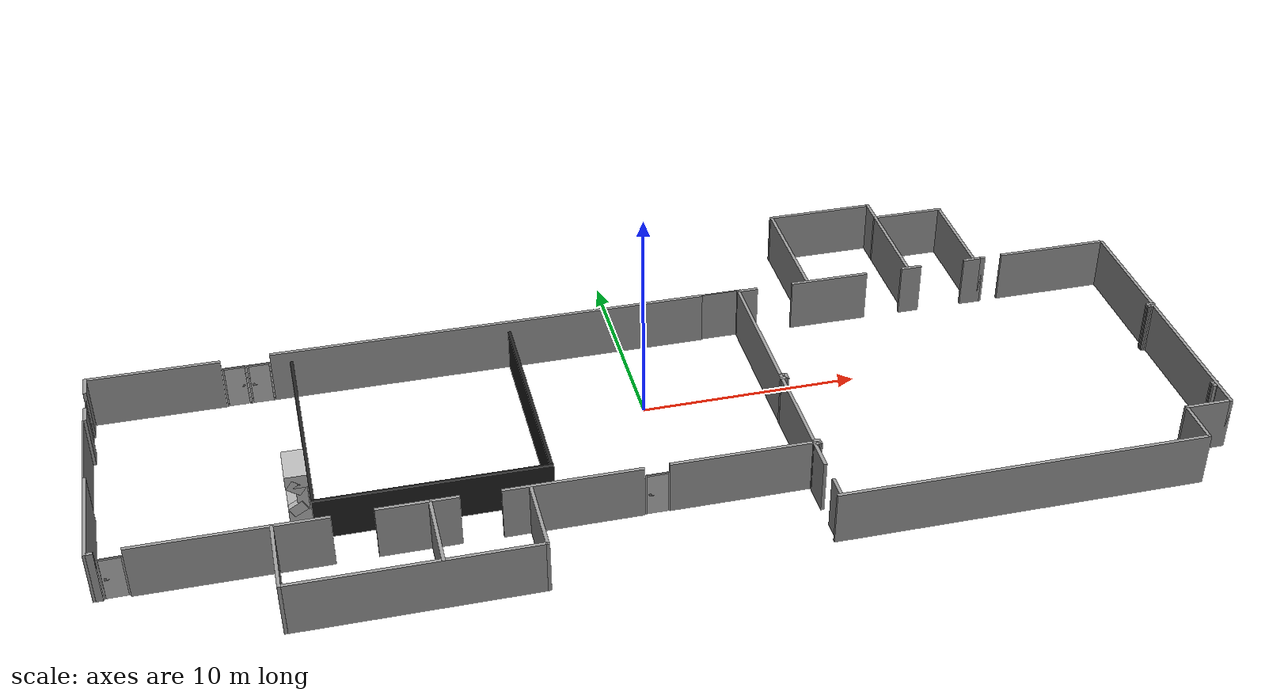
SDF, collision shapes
<?xml version='1.0'?>
<sdf version='1.6'>
  <model name='NCFM_model_v2'>
    <link name='Wall_100'>
      <pose frame=''>24.3097 -7.20486 0 0 -0 3.13225</pose>
      <self_collide>0</self_collide>
      <enable_wind>0</enable_wind>
      <kinematic>0</kinematic>
      <visual name='Wall_100_Visual'>
        <pose frame=''>0 0 1.25 0 -0 0</pose>
        <geometry>
          <box>
            <size>0.356816 0.15 2.5</size>
          </box>
        </geometry>
        <material>
          <script>
            <uri>file://media/materials/scripts/gazebo.material</uri>
            <name>Gazebo/Grey</name>
          </script>
          <ambient>1 1 1 1</ambient>
        </material>
        <meta>
          <layer>0</layer>
        </meta>
        <transparency>0</transparency>
        <cast_shadows>1</cast_shadows>
      </visual>
      <collision name='Wall_100_Collision'>
        <laser_retro>0</laser_retro>
        <max_contacts>10</max_contacts>
        <pose frame=''>0 0 1.25 0 -0 0</pose>
        <geometry>
          <box>
            <size>0.356816 0.15 2.5</size>
          </box>
        </geometry>
        <surface>
          <friction>
            <ode>
              <mu>1</mu>
              <mu2>1</mu2>
              <fdir1>0 0 0</fdir1>
              <slip1>0</slip1>
              <slip2>0</slip2>
            </ode>
            <torsional>
              <coefficient>1</coefficient>
              <patch_radius>0</patch_radius>
              <surface_radius>0</surface_radius>
              <use_patch_radius>1</use_patch_radius>
              <ode>
                <slip>0</slip>
              </ode>
            </torsional>
          </friction>
          <bounce>
            <restitution_coefficient>0</restitution_coefficient>
            <threshold>1e+06</threshold>
          </bounce>
          <contact>
            <collide_without_contact>0</collide_without_contact>
            <collide_without_contact_bitmask>1</collide_without_contact_bitmask>
            <collide_bitmask>1</collide_bitmask>
            <ode>
              <soft_cfm>0</soft_cfm>
              <soft_erp>0.2</soft_erp>
              <kp>1e+13</kp>
              <kd>1</kd>
              <max_vel>0.01</max_vel>
              <min_depth>0</min_depth>
            </ode>
            <bullet>
              <split_impulse>1</split_impulse>
              <split_impulse_penetration_threshold>-0.01</split_impulse_penetration_threshold>
              <soft_cfm>0</soft_cfm>
              <soft_erp>0.2</soft_erp>
              <kp>1e+13</kp>
              <kd>1</kd>
            </bullet>
          </contact>
        </surface>
      </collision>
    </link>
    <link name='Wall_101'>
      <pose frame=''>24.2063 -7.3015 0 0 0 -1.5708</pose>
      <self_collide>0</self_collide>
      <enable_wind>0</enable_wind>
      <kinematic>0</kinematic>
      <visual name='Wall_101_Visual'>
        <pose frame=''>0 0 1.25 0 -0 0</pose>
        <geometry>
          <box>
            <size>0.345364 0.15 2.5</size>
          </box>
        </geometry>
        <material>
          <script>
            <uri>file://media/materials/scripts/gazebo.material</uri>
            <name>Gazebo/Grey</name>
          </script>
          <ambient>1 1 1 1</ambient>
        </material>
        <meta>
          <layer>0</layer>
        </meta>
        <transparency>0</transparency>
        <cast_shadows>1</cast_shadows>
      </visual>
      <collision name='Wall_101_Collision'>
        <laser_retro>0</laser_retro>
        <max_contacts>10</max_contacts>
        <pose frame=''>0 0 1.25 0 -0 0</pose>
        <geometry>
          <box>
            <size>0.345364 0.15 2.5</size>
          </box>
        </geometry>
        <surface>
          <friction>
            <ode>
              <mu>1</mu>
              <mu2>1</mu2>
              <fdir1>0 0 0</fdir1>
              <slip1>0</slip1>
              <slip2>0</slip2>
            </ode>
            <torsional>
              <coefficient>1</coefficient>
              <patch_radius>0</patch_radius>
              <surface_radius>0</surface_radius>
              <use_patch_radius>1</use_patch_radius>
              <ode>
                <slip>0</slip>
              </ode>
            </torsional>
          </friction>
          <bounce>
            <restitution_coefficient>0</restitution_coefficient>
            <threshold>1e+06</threshold>
          </bounce>
          <contact>
            <collide_without_contact>0</collide_without_contact>
            <collide_without_contact_bitmask>1</collide_without_contact_bitmask>
            <collide_bitmask>1</collide_bitmask>
            <ode>
              <soft_cfm>0</soft_cfm>
              <soft_erp>0.2</soft_erp>
              <kp>1e+13</kp>
              <kd>1</kd>
              <max_vel>0.01</max_vel>
              <min_depth>0</min_depth>
            </ode>
            <bullet>
              <split_impulse>1</split_impulse>
              <split_impulse_penetration_threshold>-0.01</split_impulse_penetration_threshold>
              <soft_cfm>0</soft_cfm>
              <soft_erp>0.2</soft_erp>
              <kp>1e+13</kp>
              <kd>1</kd>
            </bullet>
          </contact>
        </surface>
      </collision>
    </link>
    <link name='Wall_102'>
      <pose frame=''>24.2952 -7.3991 0 0 -0 0</pose>
      <self_collide>0</self_collide>
      <enable_wind>0</enable_wind>
      <kinematic>0</kinematic>
      <visual name='Wall_102_Visual'>
        <pose frame=''>0 0 1.25 0 -0 0</pose>
        <geometry>
          <box>
            <size>0.327816 0.15 2.5</size>
          </box>
        </geometry>
        <material>
          <script>
            <uri>file://media/materials/scripts/gazebo.material</uri>
            <name>Gazebo/Grey</name>
          </script>
          <ambient>1 1 1 1</ambient>
        </material>
        <meta>
          <layer>0</layer>
        </meta>
        <transparency>0</transparency>
        <cast_shadows>1</cast_shadows>
      </visual>
      <collision name='Wall_102_Collision'>
        <laser_retro>0</laser_retro>
        <max_contacts>10</max_contacts>
        <pose frame=''>0 0 1.25 0 -0 0</pose>
        <geometry>
          <box>
            <size>0.327816 0.15 2.5</size>
          </box>
        </geometry>
        <surface>
          <friction>
            <ode>
              <mu>1</mu>
              <mu2>1</mu2>
              <fdir1>0 0 0</fdir1>
              <slip1>0</slip1>
              <slip2>0</slip2>
            </ode>
            <torsional>
              <coefficient>1</coefficient>
              <patch_radius>0</patch_radius>
              <surface_radius>0</surface_radius>
              <use_patch_radius>1</use_patch_radius>
              <ode>
                <slip>0</slip>
              </ode>
            </torsional>
          </friction>
          <bounce>
            <restitution_coefficient>0</restitution_coefficient>
            <threshold>1e+06</threshold>
          </bounce>
          <contact>
            <collide_without_contact>0</collide_without_contact>
            <collide_without_contact_bitmask>1</collide_without_contact_bitmask>
            <collide_bitmask>1</collide_bitmask>
            <ode>
              <soft_cfm>0</soft_cfm>
              <soft_erp>0.2</soft_erp>
              <kp>1e+13</kp>
              <kd>1</kd>
              <max_vel>0.01</max_vel>
              <min_depth>0</min_depth>
            </ode>
            <bullet>
              <split_impulse>1</split_impulse>
              <split_impulse_penetration_threshold>-0.01</split_impulse_penetration_threshold>
              <soft_cfm>0</soft_cfm>
              <soft_erp>0.2</soft_erp>
              <kp>1e+13</kp>
              <kd>1</kd>
            </bullet>
          </contact>
        </surface>
      </collision>
    </link>
    <link name='Wall_20'>
      <pose frame=''>-24.4274 -4.71668 0 0 0 -1.5708</pose>
      <self_collide>0</self_collide>
      <enable_wind>0</enable_wind>
      <kinematic>0</kinematic>
      <inertial>
        <inertia>
          <ixx>nan</ixx>
          <ixy>0</ixy>
          <ixz>0</ixz>
          <iyy>nan</iyy>
          <iyz>0</iyz>
          <izz>nan</izz>
        </inertia>
        <mass>0</mass>
        <pose frame=''>0 0 0 0 -0 0</pose>
      </inertial>
      <visual name='Wall_20_Visual'>
        <pose frame=''>0 0 1.25 0 -0 0</pose>
        <geometry>
          <box>
            <size>4.96533 0.15 2.5</size>
          </box>
        </geometry>
        <material>
          <script>
            <uri>file://media/materials/scripts/gazebo.material</uri>
            <name>Gazebo/Grey</name>
          </script>
          <ambient>1 1 1 1</ambient>
        </material>
        <meta>
          <layer>0</layer>
        </meta>
        <transparency>0</transparency>
        <cast_shadows>1</cast_shadows>
      </visual>
      <collision name='Wall_20_Collision'>
        <laser_retro>0</laser_retro>
        <max_contacts>10</max_contacts>
        <pose frame=''>0 0 1.25 0 -0 0</pose>
        <geometry>
          <box>
            <size>4.96533 0.15 2.5</size>
          </box>
        </geometry>
        <surface>
          <friction>
            <ode>
              <mu>1</mu>
              <mu2>1</mu2>
              <fdir1>0 0 0</fdir1>
              <slip1>0</slip1>
              <slip2>0</slip2>
            </ode>
            <torsional>
              <coefficient>1</coefficient>
              <patch_radius>0</patch_radius>
              <surface_radius>0</surface_radius>
              <use_patch_radius>1</use_patch_radius>
              <ode>
                <slip>0</slip>
              </ode>
            </torsional>
          </friction>
          <bounce>
            <restitution_coefficient>0</restitution_coefficient>
            <threshold>1e+06</threshold>
          </bounce>
          <contact>
            <collide_without_contact>0</collide_without_contact>
            <collide_without_contact_bitmask>1</collide_without_contact_bitmask>
            <collide_bitmask>1</collide_bitmask>
            <ode>
              <soft_cfm>0</soft_cfm>
              <soft_erp>0.2</soft_erp>
              <kp>1e+13</kp>
              <kd>1</kd>
              <max_vel>0.01</max_vel>
              <min_depth>0</min_depth>
            </ode>
            <bullet>
              <split_impulse>1</split_impulse>
              <split_impulse_penetration_threshold>-0.01</split_impulse_penetration_threshold>
              <soft_cfm>0</soft_cfm>
              <soft_erp>0.2</soft_erp>
              <kp>1e+13</kp>
              <kd>1</kd>
            </bullet>
          </contact>
        </surface>
      </collision>
    </link>
    <link name='Wall_23'>
      <pose frame=''>-24.2377 -7.12479 0 0 0 -0.002419</pose>
      <self_collide>0</self_collide>
      <enable_wind>0</enable_wind>
      <kinematic>0</kinematic>
      <inertial>
        <inertia>
          <ixx>nan</ixx>
          <ixy>0</ixy>
          <ixz>0</ixz>
          <iyy>nan</iyy>
          <iyz>0</iyz>
          <izz>nan</izz>
        </inertia>
        <mass>0</mass>
        <pose frame=''>0 0 0 0 -0 0</pose>
      </inertial>
      <visual name='Wall_23_Visual'>
        <pose frame=''>0 0 1.25 0 -0 0</pose>
        <geometry>
          <box>
            <size>0.295413 0.15 2.5</size>
          </box>
        </geometry>
        <material>
          <script>
            <uri>file://media/materials/scripts/gazebo.material</uri>
            <name>Gazebo/Grey</name>
          </script>
          <ambient>1 1 1 1</ambient>
        </material>
        <meta>
          <layer>0</layer>
        </meta>
        <transparency>0</transparency>
        <cast_shadows>1</cast_shadows>
      </visual>
      <collision name='Wall_23_Collision'>
        <laser_retro>0</laser_retro>
        <max_contacts>10</max_contacts>
        <pose frame=''>0 0 1.25 0 -0 0</pose>
        <geometry>
          <box>
            <size>0.295413 0.15 2.5</size>
          </box>
        </geometry>
        <surface>
          <friction>
            <ode>
              <mu>1</mu>
              <mu2>1</mu2>
              <fdir1>0 0 0</fdir1>
              <slip1>0</slip1>
              <slip2>0</slip2>
            </ode>
            <torsional>
              <coefficient>1</coefficient>
              <patch_radius>0</patch_radius>
              <surface_radius>0</surface_radius>
              <use_patch_radius>1</use_patch_radius>
              <ode>
                <slip>0</slip>
              </ode>
            </torsional>
          </friction>
          <bounce>
            <restitution_coefficient>0</restitution_coefficient>
            <threshold>1e+06</threshold>
          </bounce>
          <contact>
            <collide_without_contact>0</collide_without_contact>
            <collide_without_contact_bitmask>1</collide_without_contact_bitmask>
            <collide_bitmask>1</collide_bitmask>
            <ode>
              <soft_cfm>0</soft_cfm>
              <soft_erp>0.2</soft_erp>
              <kp>1e+13</kp>
              <kd>1</kd>
              <max_vel>0.01</max_vel>
              <min_depth>0</min_depth>
            </ode>
            <bullet>
              <split_impulse>1</split_impulse>
              <split_impulse_penetration_threshold>-0.01</split_impulse_penetration_threshold>
              <soft_cfm>0</soft_cfm>
              <soft_erp>0.2</soft_erp>
              <kp>1e+13</kp>
              <kd>1</kd>
            </bullet>
          </contact>
        </surface>
      </collision>
    </link>
    <link name='Wall_25'>
      <pose frame=''>-18.8663 -7.12561 0 0 -0 0</pose>
      <self_collide>0</self_collide>
      <enable_wind>0</enable_wind>
      <kinematic>0</kinematic>
      <visual name='Wall_25_Visual'>
        <pose frame=''>0 0 1.25 0 -0 0</pose>
        <geometry>
          <box>
            <size>8.25 0.15 2.5</size>
          </box>
        </geometry>
        <material>
          <script>
            <uri>file://media/materials/scripts/gazebo.material</uri>
            <name>Gazebo/Grey</name>
          </script>
          <ambient>1 1 1 1</ambient>
        </material>
        <meta>
          <layer>0</layer>
        </meta>
        <transparency>0</transparency>
        <cast_shadows>1</cast_shadows>
      </visual>
      <collision name='Wall_25_Collision'>
        <laser_retro>0</laser_retro>
        <max_contacts>10</max_contacts>
        <pose frame=''>0 0 1.25 0 -0 0</pose>
        <geometry>
          <box>
            <size>8.25 0.15 2.5</size>
          </box>
        </geometry>
        <surface>
          <friction>
            <ode>
              <mu>1</mu>
              <mu2>1</mu2>
              <fdir1>0 0 0</fdir1>
              <slip1>0</slip1>
              <slip2>0</slip2>
            </ode>
            <torsional>
              <coefficient>1</coefficient>
              <patch_radius>0</patch_radius>
              <surface_radius>0</surface_radius>
              <use_patch_radius>1</use_patch_radius>
              <ode>
                <slip>0</slip>
              </ode>
            </torsional>
          </friction>
          <bounce>
            <restitution_coefficient>0</restitution_coefficient>
            <threshold>1e+06</threshold>
          </bounce>
          <contact>
            <collide_without_contact>0</collide_without_contact>
            <collide_without_contact_bitmask>1</collide_without_contact_bitmask>
            <collide_bitmask>1</collide_bitmask>
            <ode>
              <soft_cfm>0</soft_cfm>
              <soft_erp>0.2</soft_erp>
              <kp>1e+13</kp>
              <kd>1</kd>
              <max_vel>0.01</max_vel>
              <min_depth>0</min_depth>
            </ode>
            <bullet>
              <split_impulse>1</split_impulse>
              <split_impulse_penetration_threshold>-0.01</split_impulse_penetration_threshold>
              <soft_cfm>0</soft_cfm>
              <soft_erp>0.2</soft_erp>
              <kp>1e+13</kp>
              <kd>1</kd>
            </bullet>
          </contact>
        </surface>
      </collision>
    </link>
    <link name='Wall_27'>
      <pose frame=''>-11.2156 -7.09196 0 0 -0 0</pose>
      <self_collide>0</self_collide>
      <enable_wind>0</enable_wind>
      <kinematic>0</kinematic>
      <visual name='Wall_27_Visual'>
        <pose frame=''>0 0 1.25 0 -0 0</pose>
        <geometry>
          <box>
            <size>3.5 0.15 2.5</size>
          </box>
        </geometry>
        <material>
          <script>
            <uri>file://media/materials/scripts/gazebo.material</uri>
            <name>Gazebo/Grey</name>
          </script>
          <ambient>1 1 1 1</ambient>
        </material>
        <meta>
          <layer>0</layer>
        </meta>
        <transparency>0</transparency>
        <cast_shadows>1</cast_shadows>
      </visual>
      <collision name='Wall_27_Collision'>
        <laser_retro>0</laser_retro>
        <max_contacts>10</max_contacts>
        <pose frame=''>0 0 1.25 0 -0 0</pose>
        <geometry>
          <box>
            <size>3.5 0.15 2.5</size>
          </box>
        </geometry>
        <surface>
          <friction>
            <ode>
              <mu>1</mu>
              <mu2>1</mu2>
              <fdir1>0 0 0</fdir1>
              <slip1>0</slip1>
              <slip2>0</slip2>
            </ode>
            <torsional>
              <coefficient>1</coefficient>
              <patch_radius>0</patch_radius>
              <surface_radius>0</surface_radius>
              <use_patch_radius>1</use_patch_radius>
              <ode>
                <slip>0</slip>
              </ode>
            </torsional>
          </friction>
          <bounce>
            <restitution_coefficient>0</restitution_coefficient>
            <threshold>1e+06</threshold>
          </bounce>
          <contact>
            <collide_without_contact>0</collide_without_contact>
            <collide_without_contact_bitmask>1</collide_without_contact_bitmask>
            <collide_bitmask>1</collide_bitmask>
            <ode>
              <soft_cfm>0</soft_cfm>
              <soft_erp>0.2</soft_erp>
              <kp>1e+13</kp>
              <kd>1</kd>
              <max_vel>0.01</max_vel>
              <min_depth>0</min_depth>
            </ode>
            <bullet>
              <split_impulse>1</split_impulse>
              <split_impulse_penetration_threshold>-0.01</split_impulse_penetration_threshold>
              <soft_cfm>0</soft_cfm>
              <soft_erp>0.2</soft_erp>
              <kp>1e+13</kp>
              <kd>1</kd>
            </bullet>
          </contact>
        </surface>
      </collision>
    </link>
    <link name='Wall_27_clone_0'>
      <pose frame=''>-15.3425 -0.297283 0 0 0 -1.57045</pose>
      <self_collide>0</self_collide>
      <enable_wind>0</enable_wind>
      <kinematic>0</kinematic>
      <gravity>1</gravity>
      <inertial>
        <mass>1</mass>
        <pose frame=''>0 0 0 0 -0 0</pose>
        <inertia>
          <ixx>1</ixx>
          <ixy>0</ixy>
          <ixz>0</ixz>
          <iyy>1</iyy>
          <iyz>0</iyz>
          <izz>1</izz>
        </inertia>
      </inertial>
      <visual name='Wall_27_Visual'>
        <pose frame=''>0 0 1 0 -0 0</pose>
        <geometry>
          <box>
            <size>10.1 0.15 2</size>
          </box>
        </geometry>
        <material>
          <script>
            <uri>file://media/materials/scripts/gazebo.material</uri>
            <name>Gazebo/FlatBlack</name>
          </script>
          <ambient>1 1 1 1</ambient>
          <shader type='vertex'>
            <normal_map>__default__</normal_map>
          </shader>
          <diffuse>0.1 0.1 0.1 1</diffuse>
          <specular>0.01 0.01 0.01 1</specular>
          <emissive>0 0 0 1</emissive>
        </material>
        <meta>
          <layer>0</layer>
        </meta>
        <transparency>0</transparency>
        <cast_shadows>1</cast_shadows>
      </visual>
      <collision name='Wall_27_Collision'>
        <laser_retro>0</laser_retro>
        <max_contacts>10</max_contacts>
        <pose frame=''>0 0 1 0 -0 0</pose>
        <geometry>
          <box>
            <size>10.1 0.15 2</size>
          </box>
        </geometry>
        <surface>
          <friction>
            <ode>
              <mu>1</mu>
              <mu2>1</mu2>
              <fdir1>0 0 0</fdir1>
              <slip1>0</slip1>
              <slip2>0</slip2>
            </ode>
            <torsional>
              <coefficient>1</coefficient>
              <patch_radius>0</patch_radius>
              <surface_radius>0</surface_radius>
              <use_patch_radius>1</use_patch_radius>
              <ode>
                <slip>0</slip>
              </ode>
            </torsional>
          </friction>
          <bounce>
            <restitution_coefficient>0</restitution_coefficient>
            <threshold>1e+06</threshold>
          </bounce>
          <contact>
            <collide_without_contact>0</collide_without_contact>
            <collide_without_contact_bitmask>1</collide_without_contact_bitmask>
            <collide_bitmask>1</collide_bitmask>
            <ode>
              <soft_cfm>0</soft_cfm>
              <soft_erp>0.2</soft_erp>
              <kp>1e+13</kp>
              <kd>1</kd>
              <max_vel>0.01</max_vel>
              <min_depth>0</min_depth>
            </ode>
            <bullet>
              <split_impulse>1</split_impulse>
              <split_impulse_penetration_threshold>-0.01</split_impulse_penetration_threshold>
              <soft_cfm>0</soft_cfm>
              <soft_erp>0.2</soft_erp>
              <kp>1e+13</kp>
              <kd>1</kd>
            </bullet>
          </contact>
        </surface>
      </collision>
    </link>
    <link name='Wall_27_clone_0_clone'>
      <pose frame=''>-10.3148 -5.42065 0 0 0 -3.14113</pose>
      <self_collide>0</self_collide>
      <enable_wind>0</enable_wind>
      <kinematic>0</kinematic>
      <gravity>1</gravity>
      <inertial>
        <mass>1</mass>
        <pose frame=''>0 0 0 0 -0 0</pose>
        <inertia>
          <ixx>1</ixx>
          <ixy>0</ixy>
          <ixz>0</ixz>
          <iyy>1</iyy>
          <iyz>0</iyz>
          <izz>1</izz>
        </inertia>
      </inertial>
      <visual name='Wall_27_Visual'>
        <pose frame=''>0 0 1 0 -0 0</pose>
        <geometry>
          <box>
            <size>10.2 0.15 2</size>
          </box>
        </geometry>
        <material>
          <script>
            <uri>file://media/materials/scripts/gazebo.material</uri>
            <name>Gazebo/FlatBlack</name>
          </script>
          <ambient>1 1 1 1</ambient>
          <shader type='vertex'>
            <normal_map>__default__</normal_map>
          </shader>
          <diffuse>0.1 0.1 0.1 1</diffuse>
          <specular>0.01 0.01 0.01 1</specular>
          <emissive>0 0 0 1</emissive>
        </material>
        <meta>
          <layer>0</layer>
        </meta>
        <transparency>0</transparency>
        <cast_shadows>1</cast_shadows>
      </visual>
      <collision name='Wall_27_Collision'>
        <laser_retro>0</laser_retro>
        <max_contacts>10</max_contacts>
        <pose frame=''>0 0 1.05 0 -0 0</pose>
        <geometry>
          <box>
            <size>10.2 0.15 2</size>
          </box>
        </geometry>
        <surface>
          <friction>
            <ode>
              <mu>1</mu>
              <mu2>1</mu2>
              <fdir1>0 0 0</fdir1>
              <slip1>0</slip1>
              <slip2>0</slip2>
            </ode>
            <torsional>
              <coefficient>1</coefficient>
              <patch_radius>0</patch_radius>
              <surface_radius>0</surface_radius>
              <use_patch_radius>1</use_patch_radius>
              <ode>
                <slip>0</slip>
              </ode>
            </torsional>
          </friction>
          <bounce>
            <restitution_coefficient>0</restitution_coefficient>
            <threshold>1e+06</threshold>
          </bounce>
          <contact>
            <collide_without_contact>0</collide_without_contact>
            <collide_without_contact_bitmask>1</collide_without_contact_bitmask>
            <collide_bitmask>1</collide_bitmask>
            <ode>
              <soft_cfm>0</soft_cfm>
              <soft_erp>0.2</soft_erp>
              <kp>1e+13</kp>
              <kd>1</kd>
              <max_vel>0.01</max_vel>
              <min_depth>0</min_depth>
            </ode>
            <bullet>
              <split_impulse>1</split_impulse>
              <split_impulse_penetration_threshold>-0.01</split_impulse_penetration_threshold>
              <soft_cfm>0</soft_cfm>
              <soft_erp>0.2</soft_erp>
              <kp>1e+13</kp>
              <kd>1</kd>
            </bullet>
          </contact>
        </surface>
      </collision>
    </link>
    <link name='Wall_27_clone_0_clone_clone'>
      <pose frame=''>-5.29471 -0.293056 0 0 0 -1.57045</pose>
      <self_collide>0</self_collide>
      <enable_wind>0</enable_wind>
      <kinematic>0</kinematic>
      <gravity>1</gravity>
      <inertial>
        <mass>1</mass>
        <pose frame=''>0 0 0 0 -0 0</pose>
        <inertia>
          <ixx>1</ixx>
          <ixy>0</ixy>
          <ixz>0</ixz>
          <iyy>1</iyy>
          <iyz>0</iyz>
          <izz>1</izz>
        </inertia>
      </inertial>
      <visual name='Wall_27_Visual'>
        <pose frame=''>0 0 1 0 -0 0</pose>
        <geometry>
          <box>
            <size>10.1 0.15 2</size>
          </box>
        </geometry>
        <material>
          <script>
            <uri>file://media/materials/scripts/gazebo.material</uri>
            <name>Gazebo/FlatBlack</name>
          </script>
          <ambient>1 1 1 1</ambient>
          <shader type='vertex'>
            <normal_map>__default__</normal_map>
          </shader>
          <diffuse>0.1 0.1 0.1 1</diffuse>
          <specular>0.01 0.01 0.01 1</specular>
          <emissive>0 0 0 1</emissive>
        </material>
        <meta>
          <layer>0</layer>
        </meta>
        <transparency>0</transparency>
        <cast_shadows>1</cast_shadows>
      </visual>
      <collision name='Wall_27_Collision'>
        <laser_retro>0</laser_retro>
        <max_contacts>10</max_contacts>
        <pose frame=''>0 0 1 0 -0 0</pose>
        <geometry>
          <box>
            <size>10.1 0.15 2</size>
          </box>
        </geometry>
        <surface>
          <friction>
            <ode>
              <mu>1</mu>
              <mu2>1</mu2>
              <fdir1>0 0 0</fdir1>
              <slip1>0</slip1>
              <slip2>0</slip2>
            </ode>
            <torsional>
              <coefficient>1</coefficient>
              <patch_radius>0</patch_radius>
              <surface_radius>0</surface_radius>
              <use_patch_radius>1</use_patch_radius>
              <ode>
                <slip>0</slip>
              </ode>
            </torsional>
          </friction>
          <bounce>
            <restitution_coefficient>0</restitution_coefficient>
            <threshold>1e+06</threshold>
          </bounce>
          <contact>
            <collide_without_contact>0</collide_without_contact>
            <collide_without_contact_bitmask>1</collide_without_contact_bitmask>
            <collide_bitmask>1</collide_bitmask>
            <ode>
              <soft_cfm>0</soft_cfm>
              <soft_erp>0.2</soft_erp>
              <kp>1e+13</kp>
              <kd>1</kd>
              <max_vel>0.01</max_vel>
              <min_depth>0</min_depth>
            </ode>
            <bullet>
              <split_impulse>1</split_impulse>
              <split_impulse_penetration_threshold>-0.01</split_impulse_penetration_threshold>
              <soft_cfm>0</soft_cfm>
              <soft_erp>0.2</soft_erp>
              <kp>1e+13</kp>
              <kd>1</kd>
            </bullet>
          </contact>
        </surface>
      </collision>
    </link>
    <link name='Wall_29'>
      <pose frame=''>-17.1074 -8.98423 0 0 -0 1.5708</pose>
      <self_collide>0</self_collide>
      <enable_wind>0</enable_wind>
      <kinematic>0</kinematic>
      <visual name='Wall_29_Visual'>
        <pose frame=''>0 0 1.25 0 -0 0</pose>
        <geometry>
          <box>
            <size>3.75 0.15 2.5</size>
          </box>
        </geometry>
        <material>
          <script>
            <uri>file://media/materials/scripts/gazebo.material</uri>
            <name>Gazebo/Grey</name>
          </script>
          <ambient>1 1 1 1</ambient>
        </material>
        <meta>
          <layer>0</layer>
        </meta>
        <transparency>0</transparency>
        <cast_shadows>1</cast_shadows>
      </visual>
      <collision name='Wall_29_Collision'>
        <laser_retro>0</laser_retro>
        <max_contacts>10</max_contacts>
        <pose frame=''>0 0 1.25 0 -0 0</pose>
        <geometry>
          <box>
            <size>3.75 0.15 2.5</size>
          </box>
        </geometry>
        <surface>
          <friction>
            <ode>
              <mu>1</mu>
              <mu2>1</mu2>
              <fdir1>0 0 0</fdir1>
              <slip1>0</slip1>
              <slip2>0</slip2>
            </ode>
            <torsional>
              <coefficient>1</coefficient>
              <patch_radius>0</patch_radius>
              <surface_radius>0</surface_radius>
              <use_patch_radius>1</use_patch_radius>
              <ode>
                <slip>0</slip>
              </ode>
            </torsional>
          </friction>
          <bounce>
            <restitution_coefficient>0</restitution_coefficient>
            <threshold>1e+06</threshold>
          </bounce>
          <contact>
            <collide_without_contact>0</collide_without_contact>
            <collide_without_contact_bitmask>1</collide_without_contact_bitmask>
            <collide_bitmask>1</collide_bitmask>
            <ode>
              <soft_cfm>0</soft_cfm>
              <soft_erp>0.2</soft_erp>
              <kp>1e+13</kp>
              <kd>1</kd>
              <max_vel>0.01</max_vel>
              <min_depth>0</min_depth>
            </ode>
            <bullet>
              <split_impulse>1</split_impulse>
              <split_impulse_penetration_threshold>-0.01</split_impulse_penetration_threshold>
              <soft_cfm>0</soft_cfm>
              <soft_erp>0.2</soft_erp>
              <kp>1e+13</kp>
              <kd>1</kd>
            </bullet>
          </contact>
        </surface>
      </collision>
    </link>
    <link name='Wall_31'>
      <pose frame=''>-11.8074 -10.7842 0 0 -0 0</pose>
      <self_collide>0</self_collide>
      <enable_wind>0</enable_wind>
      <kinematic>0</kinematic>
      <visual name='Wall_31_Visual'>
        <pose frame=''>0 0 1.25 0 -0 0</pose>
        <geometry>
          <box>
            <size>10.75 0.15 2.5</size>
          </box>
        </geometry>
        <material>
          <script>
            <uri>file://media/materials/scripts/gazebo.material</uri>
            <name>Gazebo/Grey</name>
          </script>
          <ambient>1 1 1 1</ambient>
        </material>
        <meta>
          <layer>0</layer>
        </meta>
        <transparency>0</transparency>
        <cast_shadows>1</cast_shadows>
      </visual>
      <collision name='Wall_31_Collision'>
        <laser_retro>0</laser_retro>
        <max_contacts>10</max_contacts>
        <pose frame=''>0 0 1.25 0 -0 0</pose>
        <geometry>
          <box>
            <size>10.75 0.15 2.5</size>
          </box>
        </geometry>
        <surface>
          <friction>
            <ode>
              <mu>1</mu>
              <mu2>1</mu2>
              <fdir1>0 0 0</fdir1>
              <slip1>0</slip1>
              <slip2>0</slip2>
            </ode>
            <torsional>
              <coefficient>1</coefficient>
              <patch_radius>0</patch_radius>
              <surface_radius>0</surface_radius>
              <use_patch_radius>1</use_patch_radius>
              <ode>
                <slip>0</slip>
              </ode>
            </torsional>
          </friction>
          <bounce>
            <restitution_coefficient>0</restitution_coefficient>
            <threshold>1e+06</threshold>
          </bounce>
          <contact>
            <collide_without_contact>0</collide_without_contact>
            <collide_without_contact_bitmask>1</collide_without_contact_bitmask>
            <collide_bitmask>1</collide_bitmask>
            <ode>
              <soft_cfm>0</soft_cfm>
              <soft_erp>0.2</soft_erp>
              <kp>1e+13</kp>
              <kd>1</kd>
              <max_vel>0.01</max_vel>
              <min_depth>0</min_depth>
            </ode>
            <bullet>
              <split_impulse>1</split_impulse>
              <split_impulse_penetration_threshold>-0.01</split_impulse_penetration_threshold>
              <soft_cfm>0</soft_cfm>
              <soft_erp>0.2</soft_erp>
              <kp>1e+13</kp>
              <kd>1</kd>
            </bullet>
          </contact>
        </surface>
      </collision>
    </link>
    <link name='Wall_32'>
      <pose frame=''>-6.50741 -10.7842 0 0 -0 0</pose>
      <self_collide>0</self_collide>
      <enable_wind>0</enable_wind>
      <kinematic>0</kinematic>
      <visual name='Wall_32_Visual'>
        <pose frame=''>0 0 1.25 0 -0 0</pose>
        <geometry>
          <box>
            <size>0.15 0.15 2.5</size>
          </box>
        </geometry>
        <material>
          <script>
            <uri>file://media/materials/scripts/gazebo.material</uri>
            <name>Gazebo/Grey</name>
          </script>
          <ambient>1 1 1 1</ambient>
        </material>
        <meta>
          <layer>0</layer>
        </meta>
        <transparency>0</transparency>
        <cast_shadows>1</cast_shadows>
      </visual>
      <collision name='Wall_32_Collision'>
        <laser_retro>0</laser_retro>
        <max_contacts>10</max_contacts>
        <pose frame=''>0 0 1.25 0 -0 0</pose>
        <geometry>
          <box>
            <size>0.15 0.15 2.5</size>
          </box>
        </geometry>
        <surface>
          <friction>
            <ode>
              <mu>1</mu>
              <mu2>1</mu2>
              <fdir1>0 0 0</fdir1>
              <slip1>0</slip1>
              <slip2>0</slip2>
            </ode>
            <torsional>
              <coefficient>1</coefficient>
              <patch_radius>0</patch_radius>
              <surface_radius>0</surface_radius>
              <use_patch_radius>1</use_patch_radius>
              <ode>
                <slip>0</slip>
              </ode>
            </torsional>
          </friction>
          <bounce>
            <restitution_coefficient>0</restitution_coefficient>
            <threshold>1e+06</threshold>
          </bounce>
          <contact>
            <collide_without_contact>0</collide_without_contact>
            <collide_without_contact_bitmask>1</collide_without_contact_bitmask>
            <collide_bitmask>1</collide_bitmask>
            <ode>
              <soft_cfm>0</soft_cfm>
              <soft_erp>0.2</soft_erp>
              <kp>1e+13</kp>
              <kd>1</kd>
              <max_vel>0.01</max_vel>
              <min_depth>0</min_depth>
            </ode>
            <bullet>
              <split_impulse>1</split_impulse>
              <split_impulse_penetration_threshold>-0.01</split_impulse_penetration_threshold>
              <soft_cfm>0</soft_cfm>
              <soft_erp>0.2</soft_erp>
              <kp>1e+13</kp>
              <kd>1</kd>
            </bullet>
          </contact>
        </surface>
      </collision>
    </link>
    <link name='Wall_33'>
      <pose frame=''>-6.50741 -8.98423 0 0 -0 1.5708</pose>
      <self_collide>0</self_collide>
      <enable_wind>0</enable_wind>
      <kinematic>0</kinematic>
      <visual name='Wall_33_Visual'>
        <pose frame=''>0 0 1.25 0 -0 0</pose>
        <geometry>
          <box>
            <size>3.75 0.15 2.5</size>
          </box>
        </geometry>
        <material>
          <script>
            <uri>file://media/materials/scripts/gazebo.material</uri>
            <name>Gazebo/Grey</name>
          </script>
          <ambient>1 1 1 1</ambient>
        </material>
        <meta>
          <layer>0</layer>
        </meta>
        <transparency>0</transparency>
        <cast_shadows>1</cast_shadows>
      </visual>
      <collision name='Wall_33_Collision'>
        <laser_retro>0</laser_retro>
        <max_contacts>10</max_contacts>
        <pose frame=''>0 0 1.25 0 -0 0</pose>
        <geometry>
          <box>
            <size>3.75 0.15 2.5</size>
          </box>
        </geometry>
        <surface>
          <friction>
            <ode>
              <mu>1</mu>
              <mu2>1</mu2>
              <fdir1>0 0 0</fdir1>
              <slip1>0</slip1>
              <slip2>0</slip2>
            </ode>
            <torsional>
              <coefficient>1</coefficient>
              <patch_radius>0</patch_radius>
              <surface_radius>0</surface_radius>
              <use_patch_radius>1</use_patch_radius>
              <ode>
                <slip>0</slip>
              </ode>
            </torsional>
          </friction>
          <bounce>
            <restitution_coefficient>0</restitution_coefficient>
            <threshold>1e+06</threshold>
          </bounce>
          <contact>
            <collide_without_contact>0</collide_without_contact>
            <collide_without_contact_bitmask>1</collide_without_contact_bitmask>
            <collide_bitmask>1</collide_bitmask>
            <ode>
              <soft_cfm>0</soft_cfm>
              <soft_erp>0.2</soft_erp>
              <kp>1e+13</kp>
              <kd>1</kd>
              <max_vel>0.01</max_vel>
              <min_depth>0</min_depth>
            </ode>
            <bullet>
              <split_impulse>1</split_impulse>
              <split_impulse_penetration_threshold>-0.01</split_impulse_penetration_threshold>
              <soft_cfm>0</soft_cfm>
              <soft_erp>0.2</soft_erp>
              <kp>1e+13</kp>
              <kd>1</kd>
            </bullet>
          </contact>
        </surface>
      </collision>
    </link>
    <link name='Wall_35'>
      <pose frame=''>-10.6811 -8.97448 0 0 -0 1.5708</pose>
      <self_collide>0</self_collide>
      <enable_wind>0</enable_wind>
      <kinematic>0</kinematic>
      <visual name='Wall_35_Visual'>
        <pose frame=''>0 0 1.25 0 -0 0</pose>
        <geometry>
          <box>
            <size>3.75 0.15 2.5</size>
          </box>
        </geometry>
        <material>
          <script>
            <uri>file://media/materials/scripts/gazebo.material</uri>
            <name>Gazebo/Grey</name>
          </script>
          <ambient>1 1 1 1</ambient>
        </material>
        <meta>
          <layer>0</layer>
        </meta>
        <transparency>0</transparency>
        <cast_shadows>1</cast_shadows>
      </visual>
      <collision name='Wall_35_Collision'>
        <laser_retro>0</laser_retro>
        <max_contacts>10</max_contacts>
        <pose frame=''>0 0 1.25 0 -0 0</pose>
        <geometry>
          <box>
            <size>3.75 0.15 2.5</size>
          </box>
        </geometry>
        <surface>
          <friction>
            <ode>
              <mu>1</mu>
              <mu2>1</mu2>
              <fdir1>0 0 0</fdir1>
              <slip1>0</slip1>
              <slip2>0</slip2>
            </ode>
            <torsional>
              <coefficient>1</coefficient>
              <patch_radius>0</patch_radius>
              <surface_radius>0</surface_radius>
              <use_patch_radius>1</use_patch_radius>
              <ode>
                <slip>0</slip>
              </ode>
            </torsional>
          </friction>
          <bounce>
            <restitution_coefficient>0</restitution_coefficient>
            <threshold>1e+06</threshold>
          </bounce>
          <contact>
            <collide_without_contact>0</collide_without_contact>
            <collide_without_contact_bitmask>1</collide_without_contact_bitmask>
            <collide_bitmask>1</collide_bitmask>
            <ode>
              <soft_cfm>0</soft_cfm>
              <soft_erp>0.2</soft_erp>
              <kp>1e+13</kp>
              <kd>1</kd>
              <max_vel>0.01</max_vel>
              <min_depth>0</min_depth>
            </ode>
            <bullet>
              <split_impulse>1</split_impulse>
              <split_impulse_penetration_threshold>-0.01</split_impulse_penetration_threshold>
              <soft_cfm>0</soft_cfm>
              <soft_erp>0.2</soft_erp>
              <kp>1e+13</kp>
              <kd>1</kd>
            </bullet>
          </contact>
        </surface>
      </collision>
    </link>
    <link name='Wall_37'>
      <pose frame=''>-4.69858 -7.1176 0 0 -0 0</pose>
      <self_collide>0</self_collide>
      <enable_wind>0</enable_wind>
      <kinematic>0</kinematic>
      <inertial>
        <inertia>
          <ixx>nan</ixx>
          <ixy>0</ixy>
          <ixz>0</ixz>
          <iyy>nan</iyy>
          <iyz>0</iyz>
          <izz>nan</izz>
        </inertia>
        <mass>0</mass>
        <pose frame=''>0 0 0 0 -0 0</pose>
      </inertial>
      <visual name='Wall_37_Visual'>
        <pose frame=''>0 0 1.25 0 -0 0</pose>
        <geometry>
          <box>
            <size>6.06362 0.15 2.5</size>
          </box>
        </geometry>
        <material>
          <script>
            <uri>file://media/materials/scripts/gazebo.material</uri>
            <name>Gazebo/Grey</name>
          </script>
          <ambient>1 1 1 1</ambient>
        </material>
        <meta>
          <layer>0</layer>
        </meta>
        <transparency>0</transparency>
        <cast_shadows>1</cast_shadows>
      </visual>
      <collision name='Wall_37_Collision'>
        <laser_retro>0</laser_retro>
        <max_contacts>10</max_contacts>
        <pose frame=''>0 0 1.25 0 -0 0</pose>
        <geometry>
          <box>
            <size>6.06362 0.15 2.5</size>
          </box>
        </geometry>
        <surface>
          <friction>
            <ode>
              <mu>1</mu>
              <mu2>1</mu2>
              <fdir1>0 0 0</fdir1>
              <slip1>0</slip1>
              <slip2>0</slip2>
            </ode>
            <torsional>
              <coefficient>1</coefficient>
              <patch_radius>0</patch_radius>
              <surface_radius>0</surface_radius>
              <use_patch_radius>1</use_patch_radius>
              <ode>
                <slip>0</slip>
              </ode>
            </torsional>
          </friction>
          <bounce>
            <restitution_coefficient>0</restitution_coefficient>
            <threshold>1e+06</threshold>
          </bounce>
          <contact>
            <collide_without_contact>0</collide_without_contact>
            <collide_without_contact_bitmask>1</collide_without_contact_bitmask>
            <collide_bitmask>1</collide_bitmask>
            <ode>
              <soft_cfm>0</soft_cfm>
              <soft_erp>0.2</soft_erp>
              <kp>1e+13</kp>
              <kd>1</kd>
              <max_vel>0.01</max_vel>
              <min_depth>0</min_depth>
            </ode>
            <bullet>
              <split_impulse>1</split_impulse>
              <split_impulse_penetration_threshold>-0.01</split_impulse_penetration_threshold>
              <soft_cfm>0</soft_cfm>
              <soft_erp>0.2</soft_erp>
              <kp>1e+13</kp>
              <kd>1</kd>
            </bullet>
          </contact>
        </surface>
      </collision>
    </link>
    <link name='Wall_39'>
      <pose frame=''>2.54969 -7.0981 0 0 -0 0</pose>
      <self_collide>0</self_collide>
      <enable_wind>0</enable_wind>
      <kinematic>0</kinematic>
      <visual name='Wall_39_Visual'>
        <pose frame=''>0 0 1.25 0 -0 0</pose>
        <geometry>
          <box>
            <size>6.25 0.15 2.5</size>
          </box>
        </geometry>
        <material>
          <script>
            <uri>file://media/materials/scripts/gazebo.material</uri>
            <name>Gazebo/Grey</name>
          </script>
          <ambient>1 1 1 1</ambient>
        </material>
        <meta>
          <layer>0</layer>
        </meta>
        <transparency>0</transparency>
        <cast_shadows>1</cast_shadows>
      </visual>
      <collision name='Wall_39_Collision'>
        <laser_retro>0</laser_retro>
        <max_contacts>10</max_contacts>
        <pose frame=''>0 0 1.25 0 -0 0</pose>
        <geometry>
          <box>
            <size>6.25 0.15 2.5</size>
          </box>
        </geometry>
        <surface>
          <friction>
            <ode>
              <mu>1</mu>
              <mu2>1</mu2>
              <fdir1>0 0 0</fdir1>
              <slip1>0</slip1>
              <slip2>0</slip2>
            </ode>
            <torsional>
              <coefficient>1</coefficient>
              <patch_radius>0</patch_radius>
              <surface_radius>0</surface_radius>
              <use_patch_radius>1</use_patch_radius>
              <ode>
                <slip>0</slip>
              </ode>
            </torsional>
          </friction>
          <bounce>
            <restitution_coefficient>0</restitution_coefficient>
            <threshold>1e+06</threshold>
          </bounce>
          <contact>
            <collide_without_contact>0</collide_without_contact>
            <collide_without_contact_bitmask>1</collide_without_contact_bitmask>
            <collide_bitmask>1</collide_bitmask>
            <ode>
              <soft_cfm>0</soft_cfm>
              <soft_erp>0.2</soft_erp>
              <kp>1e+13</kp>
              <kd>1</kd>
              <max_vel>0.01</max_vel>
              <min_depth>0</min_depth>
            </ode>
            <bullet>
              <split_impulse>1</split_impulse>
              <split_impulse_penetration_threshold>-0.01</split_impulse_penetration_threshold>
              <soft_cfm>0</soft_cfm>
              <soft_erp>0.2</soft_erp>
              <kp>1e+13</kp>
              <kd>1</kd>
            </bullet>
          </contact>
        </surface>
      </collision>
    </link>
    <link name='Wall_42'>
      <pose frame=''>5.78982 -10.1399 0 0 0 -1.5708</pose>
      <self_collide>0</self_collide>
      <enable_wind>0</enable_wind>
      <kinematic>0</kinematic>
      <visual name='Wall_42_Visual'>
        <pose frame=''>0 0 1.25 0 -0 0</pose>
        <geometry>
          <box>
            <size>1 0.15 2.5</size>
          </box>
        </geometry>
        <material>
          <script>
            <uri>file://media/materials/scripts/gazebo.material</uri>
            <name>Gazebo/Grey</name>
          </script>
          <ambient>1 1 1 1</ambient>
        </material>
        <meta>
          <layer>0</layer>
        </meta>
        <transparency>0</transparency>
        <cast_shadows>1</cast_shadows>
      </visual>
      <collision name='Wall_42_Collision'>
        <laser_retro>0</laser_retro>
        <max_contacts>10</max_contacts>
        <pose frame=''>0 0 1.25 0 -0 0</pose>
        <geometry>
          <box>
            <size>1 0.15 2.5</size>
          </box>
        </geometry>
        <surface>
          <friction>
            <ode>
              <mu>1</mu>
              <mu2>1</mu2>
              <fdir1>0 0 0</fdir1>
              <slip1>0</slip1>
              <slip2>0</slip2>
            </ode>
            <torsional>
              <coefficient>1</coefficient>
              <patch_radius>0</patch_radius>
              <surface_radius>0</surface_radius>
              <use_patch_radius>1</use_patch_radius>
              <ode>
                <slip>0</slip>
              </ode>
            </torsional>
          </friction>
          <bounce>
            <restitution_coefficient>0</restitution_coefficient>
            <threshold>1e+06</threshold>
          </bounce>
          <contact>
            <collide_without_contact>0</collide_without_contact>
            <collide_without_contact_bitmask>1</collide_without_contact_bitmask>
            <collide_bitmask>1</collide_bitmask>
            <ode>
              <soft_cfm>0</soft_cfm>
              <soft_erp>0.2</soft_erp>
              <kp>1e+13</kp>
              <kd>1</kd>
              <max_vel>0.01</max_vel>
              <min_depth>0</min_depth>
            </ode>
            <bullet>
              <split_impulse>1</split_impulse>
              <split_impulse_penetration_threshold>-0.01</split_impulse_penetration_threshold>
              <soft_cfm>0</soft_cfm>
              <soft_erp>0.2</soft_erp>
              <kp>1e+13</kp>
              <kd>1</kd>
            </bullet>
          </contact>
        </surface>
      </collision>
    </link>
    <link name='Wall_44'>
      <pose frame=''>5.75782 -7.90417 0 0 -0 1.5708</pose>
      <self_collide>0</self_collide>
      <enable_wind>0</enable_wind>
      <kinematic>0</kinematic>
      <visual name='Wall_44_Visual'>
        <pose frame=''>0 0 1.25 0 -0 0</pose>
        <geometry>
          <box>
            <size>1.5 0.15 2.5</size>
          </box>
        </geometry>
        <material>
          <script>
            <uri>file://media/materials/scripts/gazebo.material</uri>
            <name>Gazebo/Grey</name>
          </script>
          <ambient>1 1 1 1</ambient>
        </material>
        <meta>
          <layer>0</layer>
        </meta>
        <transparency>0</transparency>
        <cast_shadows>1</cast_shadows>
      </visual>
      <collision name='Wall_44_Collision'>
        <laser_retro>0</laser_retro>
        <max_contacts>10</max_contacts>
        <pose frame=''>0 0 1.25 0 -0 0</pose>
        <geometry>
          <box>
            <size>1.5 0.15 2.5</size>
          </box>
        </geometry>
        <surface>
          <friction>
            <ode>
              <mu>1</mu>
              <mu2>1</mu2>
              <fdir1>0 0 0</fdir1>
              <slip1>0</slip1>
              <slip2>0</slip2>
            </ode>
            <torsional>
              <coefficient>1</coefficient>
              <patch_radius>0</patch_radius>
              <surface_radius>0</surface_radius>
              <use_patch_radius>1</use_patch_radius>
              <ode>
                <slip>0</slip>
              </ode>
            </torsional>
          </friction>
          <bounce>
            <restitution_coefficient>0</restitution_coefficient>
            <threshold>1e+06</threshold>
          </bounce>
          <contact>
            <collide_without_contact>0</collide_without_contact>
            <collide_without_contact_bitmask>1</collide_without_contact_bitmask>
            <collide_bitmask>1</collide_bitmask>
            <ode>
              <soft_cfm>0</soft_cfm>
              <soft_erp>0.2</soft_erp>
              <kp>1e+13</kp>
              <kd>1</kd>
              <max_vel>0.01</max_vel>
              <min_depth>0</min_depth>
            </ode>
            <bullet>
              <split_impulse>1</split_impulse>
              <split_impulse_penetration_threshold>-0.01</split_impulse_penetration_threshold>
              <soft_cfm>0</soft_cfm>
              <soft_erp>0.2</soft_erp>
              <kp>1e+13</kp>
              <kd>1</kd>
            </bullet>
          </contact>
        </surface>
      </collision>
    </link>
    <link name='Wall_45'>
      <pose frame=''>5.87483 -7.23068 0 0 0 -0.012916</pose>
      <self_collide>0</self_collide>
      <enable_wind>0</enable_wind>
      <kinematic>0</kinematic>
      <visual name='Wall_45_Visual'>
        <pose frame=''>0 0 1.25 0 -0 0</pose>
        <geometry>
          <box>
            <size>0.384037 0.15 2.5</size>
          </box>
        </geometry>
        <material>
          <script>
            <uri>file://media/materials/scripts/gazebo.material</uri>
            <name>Gazebo/Grey</name>
          </script>
          <ambient>1 1 1 1</ambient>
        </material>
        <meta>
          <layer>0</layer>
        </meta>
        <transparency>0</transparency>
        <cast_shadows>1</cast_shadows>
      </visual>
      <collision name='Wall_45_Collision'>
        <laser_retro>0</laser_retro>
        <max_contacts>10</max_contacts>
        <pose frame=''>0 0 1.25 0 -0 0</pose>
        <geometry>
          <box>
            <size>0.384037 0.15 2.5</size>
          </box>
        </geometry>
        <surface>
          <friction>
            <ode>
              <mu>1</mu>
              <mu2>1</mu2>
              <fdir1>0 0 0</fdir1>
              <slip1>0</slip1>
              <slip2>0</slip2>
            </ode>
            <torsional>
              <coefficient>1</coefficient>
              <patch_radius>0</patch_radius>
              <surface_radius>0</surface_radius>
              <use_patch_radius>1</use_patch_radius>
              <ode>
                <slip>0</slip>
              </ode>
            </torsional>
          </friction>
          <bounce>
            <restitution_coefficient>0</restitution_coefficient>
            <threshold>1e+06</threshold>
          </bounce>
          <contact>
            <collide_without_contact>0</collide_without_contact>
            <collide_without_contact_bitmask>1</collide_without_contact_bitmask>
            <collide_bitmask>1</collide_bitmask>
            <ode>
              <soft_cfm>0</soft_cfm>
              <soft_erp>0.2</soft_erp>
              <kp>1e+13</kp>
              <kd>1</kd>
              <max_vel>0.01</max_vel>
              <min_depth>0</min_depth>
            </ode>
            <bullet>
              <split_impulse>1</split_impulse>
              <split_impulse_penetration_threshold>-0.01</split_impulse_penetration_threshold>
              <soft_cfm>0</soft_cfm>
              <soft_erp>0.2</soft_erp>
              <kp>1e+13</kp>
              <kd>1</kd>
            </bullet>
          </contact>
        </surface>
      </collision>
    </link>
    <link name='Wall_46'>
      <pose frame=''>5.99184 -7.23219 0 0 -0 0</pose>
      <self_collide>0</self_collide>
      <enable_wind>0</enable_wind>
      <kinematic>0</kinematic>
      <visual name='Wall_46_Visual'>
        <pose frame=''>0 0 1.25 0 -0 0</pose>
        <geometry>
          <box>
            <size>0.15 0.15 2.5</size>
          </box>
        </geometry>
        <material>
          <script>
            <uri>file://media/materials/scripts/gazebo.material</uri>
            <name>Gazebo/Grey</name>
          </script>
          <ambient>1 1 1 1</ambient>
        </material>
        <meta>
          <layer>0</layer>
        </meta>
        <transparency>0</transparency>
        <cast_shadows>1</cast_shadows>
      </visual>
      <collision name='Wall_46_Collision'>
        <laser_retro>0</laser_retro>
        <max_contacts>10</max_contacts>
        <pose frame=''>0 0 1.25 0 -0 0</pose>
        <geometry>
          <box>
            <size>0.15 0.15 2.5</size>
          </box>
        </geometry>
        <surface>
          <friction>
            <ode>
              <mu>1</mu>
              <mu2>1</mu2>
              <fdir1>0 0 0</fdir1>
              <slip1>0</slip1>
              <slip2>0</slip2>
            </ode>
            <torsional>
              <coefficient>1</coefficient>
              <patch_radius>0</patch_radius>
              <surface_radius>0</surface_radius>
              <use_patch_radius>1</use_patch_radius>
              <ode>
                <slip>0</slip>
              </ode>
            </torsional>
          </friction>
          <bounce>
            <restitution_coefficient>0</restitution_coefficient>
            <threshold>1e+06</threshold>
          </bounce>
          <contact>
            <collide_without_contact>0</collide_without_contact>
            <collide_without_contact_bitmask>1</collide_without_contact_bitmask>
            <collide_bitmask>1</collide_bitmask>
            <ode>
              <soft_cfm>0</soft_cfm>
              <soft_erp>0.2</soft_erp>
              <kp>1e+13</kp>
              <kd>1</kd>
              <max_vel>0.01</max_vel>
              <min_depth>0</min_depth>
            </ode>
            <bullet>
              <split_impulse>1</split_impulse>
              <split_impulse_penetration_threshold>-0.01</split_impulse_penetration_threshold>
              <soft_cfm>0</soft_cfm>
              <soft_erp>0.2</soft_erp>
              <kp>1e+13</kp>
              <kd>1</kd>
            </bullet>
          </contact>
        </surface>
      </collision>
    </link>
    <link name='Wall_47'>
      <pose frame=''>5.98727 -7.12244 0 0 -0 1.61244</pose>
      <self_collide>0</self_collide>
      <enable_wind>0</enable_wind>
      <kinematic>0</kinematic>
      <visual name='Wall_47_Visual'>
        <pose frame=''>0 0 1.25 0 -0 0</pose>
        <geometry>
          <box>
            <size>0.369506 0.15 2.5</size>
          </box>
        </geometry>
        <material>
          <script>
            <uri>file://media/materials/scripts/gazebo.material</uri>
            <name>Gazebo/Grey</name>
          </script>
          <ambient>1 1 1 1</ambient>
        </material>
        <meta>
          <layer>0</layer>
        </meta>
        <transparency>0</transparency>
        <cast_shadows>1</cast_shadows>
      </visual>
      <collision name='Wall_47_Collision'>
        <laser_retro>0</laser_retro>
        <max_contacts>10</max_contacts>
        <pose frame=''>0 0 1.25 0 -0 0</pose>
        <geometry>
          <box>
            <size>0.369506 0.15 2.5</size>
          </box>
        </geometry>
        <surface>
          <friction>
            <ode>
              <mu>1</mu>
              <mu2>1</mu2>
              <fdir1>0 0 0</fdir1>
              <slip1>0</slip1>
              <slip2>0</slip2>
            </ode>
            <torsional>
              <coefficient>1</coefficient>
              <patch_radius>0</patch_radius>
              <surface_radius>0</surface_radius>
              <use_patch_radius>1</use_patch_radius>
              <ode>
                <slip>0</slip>
              </ode>
            </torsional>
          </friction>
          <bounce>
            <restitution_coefficient>0</restitution_coefficient>
            <threshold>1e+06</threshold>
          </bounce>
          <contact>
            <collide_without_contact>0</collide_without_contact>
            <collide_without_contact_bitmask>1</collide_without_contact_bitmask>
            <collide_bitmask>1</collide_bitmask>
            <ode>
              <soft_cfm>0</soft_cfm>
              <soft_erp>0.2</soft_erp>
              <kp>1e+13</kp>
              <kd>1</kd>
              <max_vel>0.01</max_vel>
              <min_depth>0</min_depth>
            </ode>
            <bullet>
              <split_impulse>1</split_impulse>
              <split_impulse_penetration_threshold>-0.01</split_impulse_penetration_threshold>
              <soft_cfm>0</soft_cfm>
              <soft_erp>0.2</soft_erp>
              <kp>1e+13</kp>
              <kd>1</kd>
            </bullet>
          </contact>
        </surface>
      </collision>
    </link>
    <link name='Wall_48'>
      <pose frame=''>5.89123 -7.01269 0 0 -0 3.14159</pose>
      <self_collide>0</self_collide>
      <enable_wind>0</enable_wind>
      <kinematic>0</kinematic>
      <visual name='Wall_48_Visual'>
        <pose frame=''>0 0 1.25 0 -0 0</pose>
        <geometry>
          <box>
            <size>0.332922 0.15 2.5</size>
          </box>
        </geometry>
        <material>
          <script>
            <uri>file://media/materials/scripts/gazebo.material</uri>
            <name>Gazebo/Grey</name>
          </script>
          <ambient>1 1 1 1</ambient>
        </material>
        <meta>
          <layer>0</layer>
        </meta>
        <transparency>0</transparency>
        <cast_shadows>1</cast_shadows>
      </visual>
      <collision name='Wall_48_Collision'>
        <laser_retro>0</laser_retro>
        <max_contacts>10</max_contacts>
        <pose frame=''>0 0 1.25 0 -0 0</pose>
        <geometry>
          <box>
            <size>0.332922 0.15 2.5</size>
          </box>
        </geometry>
        <surface>
          <friction>
            <ode>
              <mu>1</mu>
              <mu2>1</mu2>
              <fdir1>0 0 0</fdir1>
              <slip1>0</slip1>
              <slip2>0</slip2>
            </ode>
            <torsional>
              <coefficient>1</coefficient>
              <patch_radius>0</patch_radius>
              <surface_radius>0</surface_radius>
              <use_patch_radius>1</use_patch_radius>
              <ode>
                <slip>0</slip>
              </ode>
            </torsional>
          </friction>
          <bounce>
            <restitution_coefficient>0</restitution_coefficient>
            <threshold>1e+06</threshold>
          </bounce>
          <contact>
            <collide_without_contact>0</collide_without_contact>
            <collide_without_contact_bitmask>1</collide_without_contact_bitmask>
            <collide_bitmask>1</collide_bitmask>
            <ode>
              <soft_cfm>0</soft_cfm>
              <soft_erp>0.2</soft_erp>
              <kp>1e+13</kp>
              <kd>1</kd>
              <max_vel>0.01</max_vel>
              <min_depth>0</min_depth>
            </ode>
            <bullet>
              <split_impulse>1</split_impulse>
              <split_impulse_penetration_threshold>-0.01</split_impulse_penetration_threshold>
              <soft_cfm>0</soft_cfm>
              <soft_erp>0.2</soft_erp>
              <kp>1e+13</kp>
              <kd>1</kd>
            </bullet>
          </contact>
        </surface>
      </collision>
    </link>
    <link name='Wall_52'>
      <pose frame=''>5.76795 -1.16842 0 0 0 -1.5708</pose>
      <self_collide>0</self_collide>
      <enable_wind>0</enable_wind>
      <kinematic>0</kinematic>
      <visual name='Wall_52_Visual'>
        <pose frame=''>0 0 1.25 0 -0 0</pose>
        <geometry>
          <box>
            <size>12.0515 0.15 2.5</size>
          </box>
        </geometry>
        <material>
          <script>
            <uri>file://media/materials/scripts/gazebo.material</uri>
            <name>Gazebo/Grey</name>
          </script>
          <ambient>1 1 1 1</ambient>
        </material>
        <meta>
          <layer>0</layer>
        </meta>
        <transparency>0</transparency>
        <cast_shadows>1</cast_shadows>
      </visual>
      <collision name='Wall_52_Collision'>
        <laser_retro>0</laser_retro>
        <max_contacts>10</max_contacts>
        <pose frame=''>0 0 1.25 0 -0 0</pose>
        <geometry>
          <box>
            <size>12.0515 0.15 2.5</size>
          </box>
        </geometry>
        <surface>
          <friction>
            <ode>
              <mu>1</mu>
              <mu2>1</mu2>
              <fdir1>0 0 0</fdir1>
              <slip1>0</slip1>
              <slip2>0</slip2>
            </ode>
            <torsional>
              <coefficient>1</coefficient>
              <patch_radius>0</patch_radius>
              <surface_radius>0</surface_radius>
              <use_patch_radius>1</use_patch_radius>
              <ode>
                <slip>0</slip>
              </ode>
            </torsional>
          </friction>
          <bounce>
            <restitution_coefficient>0</restitution_coefficient>
            <threshold>1e+06</threshold>
          </bounce>
          <contact>
            <collide_without_contact>0</collide_without_contact>
            <collide_without_contact_bitmask>1</collide_without_contact_bitmask>
            <collide_bitmask>1</collide_bitmask>
            <ode>
              <soft_cfm>0</soft_cfm>
              <soft_erp>0.2</soft_erp>
              <kp>1e+13</kp>
              <kd>1</kd>
              <max_vel>0.01</max_vel>
              <min_depth>0</min_depth>
            </ode>
            <bullet>
              <split_impulse>1</split_impulse>
              <split_impulse_penetration_threshold>-0.01</split_impulse_penetration_threshold>
              <soft_cfm>0</soft_cfm>
              <soft_erp>0.2</soft_erp>
              <kp>1e+13</kp>
              <kd>1</kd>
            </bullet>
          </contact>
        </surface>
      </collision>
    </link>
    <link name='Wall_54'>
      <pose frame=''>5.87993 -2.12822 0 0 -0 0</pose>
      <self_collide>0</self_collide>
      <enable_wind>0</enable_wind>
      <kinematic>0</kinematic>
      <visual name='Wall_54_Visual'>
        <pose frame=''>0 0 1.25 0 -0 0</pose>
        <geometry>
          <box>
            <size>0.373952 0.15 2.5</size>
          </box>
        </geometry>
        <material>
          <script>
            <uri>file://media/materials/scripts/gazebo.material</uri>
            <name>Gazebo/Grey</name>
          </script>
          <ambient>1 1 1 1</ambient>
        </material>
        <meta>
          <layer>0</layer>
        </meta>
        <transparency>0</transparency>
        <cast_shadows>1</cast_shadows>
      </visual>
      <collision name='Wall_54_Collision'>
        <laser_retro>0</laser_retro>
        <max_contacts>10</max_contacts>
        <pose frame=''>0 0 1.25 0 -0 0</pose>
        <geometry>
          <box>
            <size>0.373952 0.15 2.5</size>
          </box>
        </geometry>
        <surface>
          <friction>
            <ode>
              <mu>1</mu>
              <mu2>1</mu2>
              <fdir1>0 0 0</fdir1>
              <slip1>0</slip1>
              <slip2>0</slip2>
            </ode>
            <torsional>
              <coefficient>1</coefficient>
              <patch_radius>0</patch_radius>
              <surface_radius>0</surface_radius>
              <use_patch_radius>1</use_patch_radius>
              <ode>
                <slip>0</slip>
              </ode>
            </torsional>
          </friction>
          <bounce>
            <restitution_coefficient>0</restitution_coefficient>
            <threshold>1e+06</threshold>
          </bounce>
          <contact>
            <collide_without_contact>0</collide_without_contact>
            <collide_without_contact_bitmask>1</collide_without_contact_bitmask>
            <collide_bitmask>1</collide_bitmask>
            <ode>
              <soft_cfm>0</soft_cfm>
              <soft_erp>0.2</soft_erp>
              <kp>1e+13</kp>
              <kd>1</kd>
              <max_vel>0.01</max_vel>
              <min_depth>0</min_depth>
            </ode>
            <bullet>
              <split_impulse>1</split_impulse>
              <split_impulse_penetration_threshold>-0.01</split_impulse_penetration_threshold>
              <soft_cfm>0</soft_cfm>
              <soft_erp>0.2</soft_erp>
              <kp>1e+13</kp>
              <kd>1</kd>
            </bullet>
          </contact>
        </surface>
      </collision>
    </link>
    <link name='Wall_55'>
      <pose frame=''>5.99191 -2.24819 0 0 0 -1.5708</pose>
      <self_collide>0</self_collide>
      <enable_wind>0</enable_wind>
      <kinematic>0</kinematic>
      <visual name='Wall_55_Visual'>
        <pose frame=''>0 0 1.25 0 -0 0</pose>
        <geometry>
          <box>
            <size>0.389949 0.15 2.5</size>
          </box>
        </geometry>
        <material>
          <script>
            <uri>file://media/materials/scripts/gazebo.material</uri>
            <name>Gazebo/Grey</name>
          </script>
          <ambient>1 1 1 1</ambient>
        </material>
        <meta>
          <layer>0</layer>
        </meta>
        <transparency>0</transparency>
        <cast_shadows>1</cast_shadows>
      </visual>
      <collision name='Wall_55_Collision'>
        <laser_retro>0</laser_retro>
        <max_contacts>10</max_contacts>
        <pose frame=''>0 0 1.25 0 -0 0</pose>
        <geometry>
          <box>
            <size>0.389949 0.15 2.5</size>
          </box>
        </geometry>
        <surface>
          <friction>
            <ode>
              <mu>1</mu>
              <mu2>1</mu2>
              <fdir1>0 0 0</fdir1>
              <slip1>0</slip1>
              <slip2>0</slip2>
            </ode>
            <torsional>
              <coefficient>1</coefficient>
              <patch_radius>0</patch_radius>
              <surface_radius>0</surface_radius>
              <use_patch_radius>1</use_patch_radius>
              <ode>
                <slip>0</slip>
              </ode>
            </torsional>
          </friction>
          <bounce>
            <restitution_coefficient>0</restitution_coefficient>
            <threshold>1e+06</threshold>
          </bounce>
          <contact>
            <collide_without_contact>0</collide_without_contact>
            <collide_without_contact_bitmask>1</collide_without_contact_bitmask>
            <collide_bitmask>1</collide_bitmask>
            <ode>
              <soft_cfm>0</soft_cfm>
              <soft_erp>0.2</soft_erp>
              <kp>1e+13</kp>
              <kd>1</kd>
              <max_vel>0.01</max_vel>
              <min_depth>0</min_depth>
            </ode>
            <bullet>
              <split_impulse>1</split_impulse>
              <split_impulse_penetration_threshold>-0.01</split_impulse_penetration_threshold>
              <soft_cfm>0</soft_cfm>
              <soft_erp>0.2</soft_erp>
              <kp>1e+13</kp>
              <kd>1</kd>
            </bullet>
          </contact>
        </surface>
      </collision>
    </link>
    <link name='Wall_56'>
      <pose frame=''>5.87193 -2.37616 0 0 0 -3.07502</pose>
      <self_collide>0</self_collide>
      <enable_wind>0</enable_wind>
      <kinematic>0</kinematic>
      <visual name='Wall_56_Visual'>
        <pose frame=''>0 0 1.25 0 -0 0</pose>
        <geometry>
          <box>
            <size>0.389949 0.15 2.5</size>
          </box>
        </geometry>
        <material>
          <script>
            <uri>file://media/materials/scripts/gazebo.material</uri>
            <name>Gazebo/Grey</name>
          </script>
          <ambient>1 1 1 1</ambient>
        </material>
        <meta>
          <layer>0</layer>
        </meta>
        <transparency>0</transparency>
        <cast_shadows>1</cast_shadows>
      </visual>
      <collision name='Wall_56_Collision'>
        <laser_retro>0</laser_retro>
        <max_contacts>10</max_contacts>
        <pose frame=''>0 0 1.25 0 -0 0</pose>
        <geometry>
          <box>
            <size>0.389949 0.15 2.5</size>
          </box>
        </geometry>
        <surface>
          <friction>
            <ode>
              <mu>1</mu>
              <mu2>1</mu2>
              <fdir1>0 0 0</fdir1>
              <slip1>0</slip1>
              <slip2>0</slip2>
            </ode>
            <torsional>
              <coefficient>1</coefficient>
              <patch_radius>0</patch_radius>
              <surface_radius>0</surface_radius>
              <use_patch_radius>1</use_patch_radius>
              <ode>
                <slip>0</slip>
              </ode>
            </torsional>
          </friction>
          <bounce>
            <restitution_coefficient>0</restitution_coefficient>
            <threshold>1e+06</threshold>
          </bounce>
          <contact>
            <collide_without_contact>0</collide_without_contact>
            <collide_without_contact_bitmask>1</collide_without_contact_bitmask>
            <collide_bitmask>1</collide_bitmask>
            <ode>
              <soft_cfm>0</soft_cfm>
              <soft_erp>0.2</soft_erp>
              <kp>1e+13</kp>
              <kd>1</kd>
              <max_vel>0.01</max_vel>
              <min_depth>0</min_depth>
            </ode>
            <bullet>
              <split_impulse>1</split_impulse>
              <split_impulse_penetration_threshold>-0.01</split_impulse_penetration_threshold>
              <soft_cfm>0</soft_cfm>
              <soft_erp>0.2</soft_erp>
              <kp>1e+13</kp>
              <kd>1</kd>
            </bullet>
          </contact>
        </surface>
      </collision>
    </link>
    <link name='Wall_58'>
      <pose frame=''>-24.3958 2.23125 0 0 -0 1.5708</pose>
      <self_collide>0</self_collide>
      <enable_wind>0</enable_wind>
      <kinematic>0</kinematic>
      <inertial>
        <inertia>
          <ixx>nan</ixx>
          <ixy>0</ixy>
          <ixz>0</ixz>
          <iyy>nan</iyy>
          <iyz>0</iyz>
          <izz>nan</izz>
        </inertia>
        <mass>0</mass>
        <pose frame=''>0 0 0 0 -0 0</pose>
      </inertial>
      <visual name='Wall_58_Visual'>
        <pose frame=''>0 0 1.25 0 -0 0</pose>
        <geometry>
          <box>
            <size>0.888827 0.15 2.5</size>
          </box>
        </geometry>
        <material>
          <script>
            <uri>file://media/materials/scripts/gazebo.material</uri>
            <name>Gazebo/Grey</name>
          </script>
          <ambient>1 1 1 1</ambient>
        </material>
        <meta>
          <layer>0</layer>
        </meta>
        <transparency>0</transparency>
        <cast_shadows>1</cast_shadows>
      </visual>
      <collision name='Wall_58_Collision'>
        <laser_retro>0</laser_retro>
        <max_contacts>10</max_contacts>
        <pose frame=''>0 0 1.25 0 -0 0</pose>
        <geometry>
          <box>
            <size>0.888827 0.15 2.5</size>
          </box>
        </geometry>
        <surface>
          <friction>
            <ode>
              <mu>1</mu>
              <mu2>1</mu2>
              <fdir1>0 0 0</fdir1>
              <slip1>0</slip1>
              <slip2>0</slip2>
            </ode>
            <torsional>
              <coefficient>1</coefficient>
              <patch_radius>0</patch_radius>
              <surface_radius>0</surface_radius>
              <use_patch_radius>1</use_patch_radius>
              <ode>
                <slip>0</slip>
              </ode>
            </torsional>
          </friction>
          <bounce>
            <restitution_coefficient>0</restitution_coefficient>
            <threshold>1e+06</threshold>
          </bounce>
          <contact>
            <collide_without_contact>0</collide_without_contact>
            <collide_without_contact_bitmask>1</collide_without_contact_bitmask>
            <collide_bitmask>1</collide_bitmask>
            <ode>
              <soft_cfm>0</soft_cfm>
              <soft_erp>0.2</soft_erp>
              <kp>1e+13</kp>
              <kd>1</kd>
              <max_vel>0.01</max_vel>
              <min_depth>0</min_depth>
            </ode>
            <bullet>
              <split_impulse>1</split_impulse>
              <split_impulse_penetration_threshold>-0.01</split_impulse_penetration_threshold>
              <soft_cfm>0</soft_cfm>
              <soft_erp>0.2</soft_erp>
              <kp>1e+13</kp>
              <kd>1</kd>
            </bullet>
          </contact>
        </surface>
      </collision>
    </link>
    <link name='Wall_61'>
      <pose frame=''>-24.3958 4.32867 0 0 -0 1.5708</pose>
      <self_collide>0</self_collide>
      <enable_wind>0</enable_wind>
      <kinematic>0</kinematic>
      <inertial>
        <inertia>
          <ixx>nan</ixx>
          <ixy>0</ixy>
          <ixz>0</ixz>
          <iyy>nan</iyy>
          <iyz>0</iyz>
          <izz>nan</izz>
        </inertia>
        <mass>0</mass>
        <pose frame=''>0 0 0 0 -0 0</pose>
      </inertial>
      <visual name='Wall_61_Visual'>
        <pose frame=''>0 0 1.25 0 -0 0</pose>
        <geometry>
          <box>
            <size>1.09696 0.15 2.5</size>
          </box>
        </geometry>
        <material>
          <script>
            <uri>file://media/materials/scripts/gazebo.material</uri>
            <name>Gazebo/Grey</name>
          </script>
          <ambient>1 1 1 1</ambient>
        </material>
        <meta>
          <layer>0</layer>
        </meta>
        <transparency>0</transparency>
        <cast_shadows>1</cast_shadows>
      </visual>
      <collision name='Wall_61_Collision'>
        <laser_retro>0</laser_retro>
        <max_contacts>10</max_contacts>
        <pose frame=''>0 0 1.25 0 -0 0</pose>
        <geometry>
          <box>
            <size>1.09696 0.15 2.5</size>
          </box>
        </geometry>
        <surface>
          <friction>
            <ode>
              <mu>1</mu>
              <mu2>1</mu2>
              <fdir1>0 0 0</fdir1>
              <slip1>0</slip1>
              <slip2>0</slip2>
            </ode>
            <torsional>
              <coefficient>1</coefficient>
              <patch_radius>0</patch_radius>
              <surface_radius>0</surface_radius>
              <use_patch_radius>1</use_patch_radius>
              <ode>
                <slip>0</slip>
              </ode>
            </torsional>
          </friction>
          <bounce>
            <restitution_coefficient>0</restitution_coefficient>
            <threshold>1e+06</threshold>
          </bounce>
          <contact>
            <collide_without_contact>0</collide_without_contact>
            <collide_without_contact_bitmask>1</collide_without_contact_bitmask>
            <collide_bitmask>1</collide_bitmask>
            <ode>
              <soft_cfm>0</soft_cfm>
              <soft_erp>0.2</soft_erp>
              <kp>1e+13</kp>
              <kd>1</kd>
              <max_vel>0.01</max_vel>
              <min_depth>0</min_depth>
            </ode>
            <bullet>
              <split_impulse>1</split_impulse>
              <split_impulse_penetration_threshold>-0.01</split_impulse_penetration_threshold>
              <soft_cfm>0</soft_cfm>
              <soft_erp>0.2</soft_erp>
              <kp>1e+13</kp>
              <kd>1</kd>
            </bullet>
          </contact>
        </surface>
      </collision>
    </link>
    <link name='Wall_62'>
      <pose frame=''>-21.4708 4.8039 0 0 -0 0</pose>
      <self_collide>0</self_collide>
      <enable_wind>0</enable_wind>
      <kinematic>0</kinematic>
      <inertial>
        <inertia>
          <ixx>nan</ixx>
          <ixy>0</ixy>
          <ixz>0</ixz>
          <iyy>nan</iyy>
          <iyz>0</iyz>
          <izz>nan</izz>
        </inertia>
        <mass>0</mass>
        <pose frame=''>0 0 0 0 -0 0</pose>
      </inertial>
      <visual name='Wall_62_Visual'>
        <pose frame=''>0 0 1.25 0 -0 0</pose>
        <geometry>
          <box>
            <size>6 0.15 2.5</size>
          </box>
        </geometry>
        <material>
          <script>
            <uri>file://media/materials/scripts/gazebo.material</uri>
            <name>Gazebo/Grey</name>
          </script>
          <ambient>1 1 1 1</ambient>
        </material>
        <meta>
          <layer>0</layer>
        </meta>
        <transparency>0</transparency>
        <cast_shadows>1</cast_shadows>
      </visual>
      <collision name='Wall_62_Collision'>
        <laser_retro>0</laser_retro>
        <max_contacts>10</max_contacts>
        <pose frame=''>0 0 1.25 0 -0 0</pose>
        <geometry>
          <box>
            <size>6 0.15 2.5</size>
          </box>
        </geometry>
        <surface>
          <friction>
            <ode>
              <mu>1</mu>
              <mu2>1</mu2>
              <fdir1>0 0 0</fdir1>
              <slip1>0</slip1>
              <slip2>0</slip2>
            </ode>
            <torsional>
              <coefficient>1</coefficient>
              <patch_radius>0</patch_radius>
              <surface_radius>0</surface_radius>
              <use_patch_radius>1</use_patch_radius>
              <ode>
                <slip>0</slip>
              </ode>
            </torsional>
          </friction>
          <bounce>
            <restitution_coefficient>0</restitution_coefficient>
            <threshold>1e+06</threshold>
          </bounce>
          <contact>
            <collide_without_contact>0</collide_without_contact>
            <collide_without_contact_bitmask>1</collide_without_contact_bitmask>
            <collide_bitmask>1</collide_bitmask>
            <ode>
              <soft_cfm>0</soft_cfm>
              <soft_erp>0.2</soft_erp>
              <kp>1e+13</kp>
              <kd>1</kd>
              <max_vel>0.01</max_vel>
              <min_depth>0</min_depth>
            </ode>
            <bullet>
              <split_impulse>1</split_impulse>
              <split_impulse_penetration_threshold>-0.01</split_impulse_penetration_threshold>
              <soft_cfm>0</soft_cfm>
              <soft_erp>0.2</soft_erp>
              <kp>1e+13</kp>
              <kd>1</kd>
            </bullet>
          </contact>
        </surface>
      </collision>
    </link>
    <link name='Wall_64'>
      <pose frame=''>-6.14881 4.8294 0 0 -0 0</pose>
      <self_collide>0</self_collide>
      <enable_wind>0</enable_wind>
      <kinematic>0</kinematic>
      <visual name='Wall_64_Visual'>
        <pose frame=''>0 0 1.25 0 -0 0</pose>
        <geometry>
          <box>
            <size>20.25 0.15 2.5</size>
          </box>
        </geometry>
        <material>
          <script>
            <uri>file://media/materials/scripts/gazebo.material</uri>
            <name>Gazebo/Grey</name>
          </script>
          <ambient>1 1 1 1</ambient>
        </material>
        <meta>
          <layer>0</layer>
        </meta>
        <transparency>0</transparency>
        <cast_shadows>1</cast_shadows>
      </visual>
      <collision name='Wall_64_Collision'>
        <laser_retro>0</laser_retro>
        <max_contacts>10</max_contacts>
        <pose frame=''>0 0 1.25 0 -0 0</pose>
        <geometry>
          <box>
            <size>20.25 0.15 2.5</size>
          </box>
        </geometry>
        <surface>
          <friction>
            <ode>
              <mu>1</mu>
              <mu2>1</mu2>
              <fdir1>0 0 0</fdir1>
              <slip1>0</slip1>
              <slip2>0</slip2>
            </ode>
            <torsional>
              <coefficient>1</coefficient>
              <patch_radius>0</patch_radius>
              <surface_radius>0</surface_radius>
              <use_patch_radius>1</use_patch_radius>
              <ode>
                <slip>0</slip>
              </ode>
            </torsional>
          </friction>
          <bounce>
            <restitution_coefficient>0</restitution_coefficient>
            <threshold>1e+06</threshold>
          </bounce>
          <contact>
            <collide_without_contact>0</collide_without_contact>
            <collide_without_contact_bitmask>1</collide_without_contact_bitmask>
            <collide_bitmask>1</collide_bitmask>
            <ode>
              <soft_cfm>0</soft_cfm>
              <soft_erp>0.2</soft_erp>
              <kp>1e+13</kp>
              <kd>1</kd>
              <max_vel>0.01</max_vel>
              <min_depth>0</min_depth>
            </ode>
            <bullet>
              <split_impulse>1</split_impulse>
              <split_impulse_penetration_threshold>-0.01</split_impulse_penetration_threshold>
              <soft_cfm>0</soft_cfm>
              <soft_erp>0.2</soft_erp>
              <kp>1e+13</kp>
              <kd>1</kd>
            </bullet>
          </contact>
        </surface>
      </collision>
    </link>
    <link name='Wall_66'>
      <pose frame=''>6.19295 4.7823 0 0 -0 0</pose>
      <self_collide>0</self_collide>
      <enable_wind>0</enable_wind>
      <kinematic>0</kinematic>
      <visual name='Wall_66_Visual'>
        <pose frame=''>0 0 1.25 0 -0 0</pose>
        <geometry>
          <box>
            <size>1 0.15 2.5</size>
          </box>
        </geometry>
        <material>
          <script>
            <uri>file://media/materials/scripts/gazebo.material</uri>
            <name>Gazebo/Grey</name>
          </script>
          <ambient>1 1 1 1</ambient>
        </material>
        <meta>
          <layer>0</layer>
        </meta>
        <transparency>0</transparency>
        <cast_shadows>1</cast_shadows>
      </visual>
      <collision name='Wall_66_Collision'>
        <laser_retro>0</laser_retro>
        <max_contacts>10</max_contacts>
        <pose frame=''>0 0 1.25 0 -0 0</pose>
        <geometry>
          <box>
            <size>1 0.15 2.5</size>
          </box>
        </geometry>
        <surface>
          <friction>
            <ode>
              <mu>1</mu>
              <mu2>1</mu2>
              <fdir1>0 0 0</fdir1>
              <slip1>0</slip1>
              <slip2>0</slip2>
            </ode>
            <torsional>
              <coefficient>1</coefficient>
              <patch_radius>0</patch_radius>
              <surface_radius>0</surface_radius>
              <use_patch_radius>1</use_patch_radius>
              <ode>
                <slip>0</slip>
              </ode>
            </torsional>
          </friction>
          <bounce>
            <restitution_coefficient>0</restitution_coefficient>
            <threshold>1e+06</threshold>
          </bounce>
          <contact>
            <collide_without_contact>0</collide_without_contact>
            <collide_without_contact_bitmask>1</collide_without_contact_bitmask>
            <collide_bitmask>1</collide_bitmask>
            <ode>
              <soft_cfm>0</soft_cfm>
              <soft_erp>0.2</soft_erp>
              <kp>1e+13</kp>
              <kd>1</kd>
              <max_vel>0.01</max_vel>
              <min_depth>0</min_depth>
            </ode>
            <bullet>
              <split_impulse>1</split_impulse>
              <split_impulse_penetration_threshold>-0.01</split_impulse_penetration_threshold>
              <soft_cfm>0</soft_cfm>
              <soft_erp>0.2</soft_erp>
              <kp>1e+13</kp>
              <kd>1</kd>
            </bullet>
          </contact>
        </surface>
      </collision>
    </link>
    <link name='Wall_68'>
      <pose frame=''>10.2993 4.80204 0 0 -0 0</pose>
      <self_collide>0</self_collide>
      <enable_wind>0</enable_wind>
      <kinematic>0</kinematic>
      <visual name='Wall_68_Visual'>
        <pose frame=''>0 0 1.25 0 -0 0</pose>
        <geometry>
          <box>
            <size>3.75 0.15 2.5</size>
          </box>
        </geometry>
        <material>
          <script>
            <uri>file://media/materials/scripts/gazebo.material</uri>
            <name>Gazebo/Grey</name>
          </script>
          <ambient>1 1 1 1</ambient>
        </material>
        <meta>
          <layer>0</layer>
        </meta>
        <transparency>0</transparency>
        <cast_shadows>1</cast_shadows>
      </visual>
      <collision name='Wall_68_Collision'>
        <laser_retro>0</laser_retro>
        <max_contacts>10</max_contacts>
        <pose frame=''>0 0 1.25 0 -0 0</pose>
        <geometry>
          <box>
            <size>3.75 0.15 2.5</size>
          </box>
        </geometry>
        <surface>
          <friction>
            <ode>
              <mu>1</mu>
              <mu2>1</mu2>
              <fdir1>0 0 0</fdir1>
              <slip1>0</slip1>
              <slip2>0</slip2>
            </ode>
            <torsional>
              <coefficient>1</coefficient>
              <patch_radius>0</patch_radius>
              <surface_radius>0</surface_radius>
              <use_patch_radius>1</use_patch_radius>
              <ode>
                <slip>0</slip>
              </ode>
            </torsional>
          </friction>
          <bounce>
            <restitution_coefficient>0</restitution_coefficient>
            <threshold>1e+06</threshold>
          </bounce>
          <contact>
            <collide_without_contact>0</collide_without_contact>
            <collide_without_contact_bitmask>1</collide_without_contact_bitmask>
            <collide_bitmask>1</collide_bitmask>
            <ode>
              <soft_cfm>0</soft_cfm>
              <soft_erp>0.2</soft_erp>
              <kp>1e+13</kp>
              <kd>1</kd>
              <max_vel>0.01</max_vel>
              <min_depth>0</min_depth>
            </ode>
            <bullet>
              <split_impulse>1</split_impulse>
              <split_impulse_penetration_threshold>-0.01</split_impulse_penetration_threshold>
              <soft_cfm>0</soft_cfm>
              <soft_erp>0.2</soft_erp>
              <kp>1e+13</kp>
              <kd>1</kd>
            </bullet>
          </contact>
        </surface>
      </collision>
    </link>
    <link name='Wall_70'>
      <pose frame=''>14.4459 4.80204 0 0 -0 0</pose>
      <self_collide>0</self_collide>
      <enable_wind>0</enable_wind>
      <kinematic>0</kinematic>
      <visual name='Wall_70_Visual'>
        <pose frame=''>0 0 1.25 0 -0 0</pose>
        <geometry>
          <box>
            <size>1 0.15 2.5</size>
          </box>
        </geometry>
        <material>
          <script>
            <uri>file://media/materials/scripts/gazebo.material</uri>
            <name>Gazebo/Grey</name>
          </script>
          <ambient>1 1 1 1</ambient>
        </material>
        <meta>
          <layer>0</layer>
        </meta>
        <transparency>0</transparency>
        <cast_shadows>1</cast_shadows>
      </visual>
      <collision name='Wall_70_Collision'>
        <laser_retro>0</laser_retro>
        <max_contacts>10</max_contacts>
        <pose frame=''>0 0 1.25 0 -0 0</pose>
        <geometry>
          <box>
            <size>1 0.15 2.5</size>
          </box>
        </geometry>
        <surface>
          <friction>
            <ode>
              <mu>1</mu>
              <mu2>1</mu2>
              <fdir1>0 0 0</fdir1>
              <slip1>0</slip1>
              <slip2>0</slip2>
            </ode>
            <torsional>
              <coefficient>1</coefficient>
              <patch_radius>0</patch_radius>
              <surface_radius>0</surface_radius>
              <use_patch_radius>1</use_patch_radius>
              <ode>
                <slip>0</slip>
              </ode>
            </torsional>
          </friction>
          <bounce>
            <restitution_coefficient>0</restitution_coefficient>
            <threshold>1e+06</threshold>
          </bounce>
          <contact>
            <collide_without_contact>0</collide_without_contact>
            <collide_without_contact_bitmask>1</collide_without_contact_bitmask>
            <collide_bitmask>1</collide_bitmask>
            <ode>
              <soft_cfm>0</soft_cfm>
              <soft_erp>0.2</soft_erp>
              <kp>1e+13</kp>
              <kd>1</kd>
              <max_vel>0.01</max_vel>
              <min_depth>0</min_depth>
            </ode>
            <bullet>
              <split_impulse>1</split_impulse>
              <split_impulse_penetration_threshold>-0.01</split_impulse_penetration_threshold>
              <soft_cfm>0</soft_cfm>
              <soft_erp>0.2</soft_erp>
              <kp>1e+13</kp>
              <kd>1</kd>
            </bullet>
          </contact>
        </surface>
      </collision>
    </link>
    <link name='Wall_72'>
      <pose frame=''>17.6403 4.80204 0 0 -0 0</pose>
      <self_collide>0</self_collide>
      <enable_wind>0</enable_wind>
      <kinematic>0</kinematic>
      <visual name='Wall_72_Visual'>
        <pose frame=''>0 0 1.25 0 -0 0</pose>
        <geometry>
          <box>
            <size>1 0.15 2.5</size>
          </box>
        </geometry>
        <material>
          <script>
            <uri>file://media/materials/scripts/gazebo.material</uri>
            <name>Gazebo/Grey</name>
          </script>
          <ambient>1 1 1 1</ambient>
        </material>
        <meta>
          <layer>0</layer>
        </meta>
        <transparency>0</transparency>
        <cast_shadows>1</cast_shadows>
      </visual>
      <collision name='Wall_72_Collision'>
        <laser_retro>0</laser_retro>
        <max_contacts>10</max_contacts>
        <pose frame=''>0 0 1.25 0 -0 0</pose>
        <geometry>
          <box>
            <size>1 0.15 2.5</size>
          </box>
        </geometry>
        <surface>
          <friction>
            <ode>
              <mu>1</mu>
              <mu2>1</mu2>
              <fdir1>0 0 0</fdir1>
              <slip1>0</slip1>
              <slip2>0</slip2>
            </ode>
            <torsional>
              <coefficient>1</coefficient>
              <patch_radius>0</patch_radius>
              <surface_radius>0</surface_radius>
              <use_patch_radius>1</use_patch_radius>
              <ode>
                <slip>0</slip>
              </ode>
            </torsional>
          </friction>
          <bounce>
            <restitution_coefficient>0</restitution_coefficient>
            <threshold>1e+06</threshold>
          </bounce>
          <contact>
            <collide_without_contact>0</collide_without_contact>
            <collide_without_contact_bitmask>1</collide_without_contact_bitmask>
            <collide_bitmask>1</collide_bitmask>
            <ode>
              <soft_cfm>0</soft_cfm>
              <soft_erp>0.2</soft_erp>
              <kp>1e+13</kp>
              <kd>1</kd>
              <max_vel>0.01</max_vel>
              <min_depth>0</min_depth>
            </ode>
            <bullet>
              <split_impulse>1</split_impulse>
              <split_impulse_penetration_threshold>-0.01</split_impulse_penetration_threshold>
              <soft_cfm>0</soft_cfm>
              <soft_erp>0.2</soft_erp>
              <kp>1e+13</kp>
              <kd>1</kd>
            </bullet>
          </contact>
        </surface>
      </collision>
    </link>
    <link name='Wall_73'>
      <pose frame=''>18.1153 4.80204 0 0 -0 0</pose>
      <self_collide>0</self_collide>
      <enable_wind>0</enable_wind>
      <kinematic>0</kinematic>
      <visual name='Wall_73_Visual'>
        <pose frame=''>0 0 1.25 0 -0 0</pose>
        <geometry>
          <box>
            <size>0.25 0.15 2.5</size>
          </box>
        </geometry>
        <material>
          <script>
            <uri>file://media/materials/scripts/gazebo.material</uri>
            <name>Gazebo/Grey</name>
          </script>
          <ambient>1 1 1 1</ambient>
        </material>
        <meta>
          <layer>0</layer>
        </meta>
        <transparency>0</transparency>
        <cast_shadows>1</cast_shadows>
      </visual>
      <collision name='Wall_73_Collision'>
        <laser_retro>0</laser_retro>
        <max_contacts>10</max_contacts>
        <pose frame=''>0 0 1.25 0 -0 0</pose>
        <geometry>
          <box>
            <size>0.25 0.15 2.5</size>
          </box>
        </geometry>
        <surface>
          <friction>
            <ode>
              <mu>1</mu>
              <mu2>1</mu2>
              <fdir1>0 0 0</fdir1>
              <slip1>0</slip1>
              <slip2>0</slip2>
            </ode>
            <torsional>
              <coefficient>1</coefficient>
              <patch_radius>0</patch_radius>
              <surface_radius>0</surface_radius>
              <use_patch_radius>1</use_patch_radius>
              <ode>
                <slip>0</slip>
              </ode>
            </torsional>
          </friction>
          <bounce>
            <restitution_coefficient>0</restitution_coefficient>
            <threshold>1e+06</threshold>
          </bounce>
          <contact>
            <collide_without_contact>0</collide_without_contact>
            <collide_without_contact_bitmask>1</collide_without_contact_bitmask>
            <collide_bitmask>1</collide_bitmask>
            <ode>
              <soft_cfm>0</soft_cfm>
              <soft_erp>0.2</soft_erp>
              <kp>1e+13</kp>
              <kd>1</kd>
              <max_vel>0.01</max_vel>
              <min_depth>0</min_depth>
            </ode>
            <bullet>
              <split_impulse>1</split_impulse>
              <split_impulse_penetration_threshold>-0.01</split_impulse_penetration_threshold>
              <soft_cfm>0</soft_cfm>
              <soft_erp>0.2</soft_erp>
              <kp>1e+13</kp>
              <kd>1</kd>
            </bullet>
          </contact>
        </surface>
      </collision>
    </link>
    <link name='Wall_75'>
      <pose frame=''>21.7116 4.82319 0 0 -0 0</pose>
      <self_collide>0</self_collide>
      <enable_wind>0</enable_wind>
      <kinematic>0</kinematic>
      <visual name='Wall_75_Visual'>
        <pose frame=''>0 0 1.25 0 -0 0</pose>
        <geometry>
          <box>
            <size>5.25 0.15 2.5</size>
          </box>
        </geometry>
        <material>
          <script>
            <uri>file://media/materials/scripts/gazebo.material</uri>
            <name>Gazebo/Grey</name>
          </script>
          <ambient>1 1 1 1</ambient>
        </material>
        <meta>
          <layer>0</layer>
        </meta>
        <transparency>0</transparency>
        <cast_shadows>1</cast_shadows>
      </visual>
      <collision name='Wall_75_Collision'>
        <laser_retro>0</laser_retro>
        <max_contacts>10</max_contacts>
        <pose frame=''>0 0 1.25 0 -0 0</pose>
        <geometry>
          <box>
            <size>5.25 0.15 2.5</size>
          </box>
        </geometry>
        <surface>
          <friction>
            <ode>
              <mu>1</mu>
              <mu2>1</mu2>
              <fdir1>0 0 0</fdir1>
              <slip1>0</slip1>
              <slip2>0</slip2>
            </ode>
            <torsional>
              <coefficient>1</coefficient>
              <patch_radius>0</patch_radius>
              <surface_radius>0</surface_radius>
              <use_patch_radius>1</use_patch_radius>
              <ode>
                <slip>0</slip>
              </ode>
            </torsional>
          </friction>
          <bounce>
            <restitution_coefficient>0</restitution_coefficient>
            <threshold>1e+06</threshold>
          </bounce>
          <contact>
            <collide_without_contact>0</collide_without_contact>
            <collide_without_contact_bitmask>1</collide_without_contact_bitmask>
            <collide_bitmask>1</collide_bitmask>
            <ode>
              <soft_cfm>0</soft_cfm>
              <soft_erp>0.2</soft_erp>
              <kp>1e+13</kp>
              <kd>1</kd>
              <max_vel>0.01</max_vel>
              <min_depth>0</min_depth>
            </ode>
            <bullet>
              <split_impulse>1</split_impulse>
              <split_impulse_penetration_threshold>-0.01</split_impulse_penetration_threshold>
              <soft_cfm>0</soft_cfm>
              <soft_erp>0.2</soft_erp>
              <kp>1e+13</kp>
              <kd>1</kd>
            </bullet>
          </contact>
        </surface>
      </collision>
    </link>
    <link name='Wall_77'>
      <pose frame=''>24.387 -1.91438 0 0 -0 1.5708</pose>
      <self_collide>0</self_collide>
      <enable_wind>0</enable_wind>
      <kinematic>0</kinematic>
      <visual name='Wall_77_Visual'>
        <pose frame=''>0 0 1.25 0 -0 0</pose>
        <geometry>
          <box>
            <size>13.5 0.15 2.5</size>
          </box>
        </geometry>
        <material>
          <script>
            <uri>file://media/materials/scripts/gazebo.material</uri>
            <name>Gazebo/Grey</name>
          </script>
          <ambient>1 1 1 1</ambient>
        </material>
        <meta>
          <layer>0</layer>
        </meta>
        <transparency>0</transparency>
        <cast_shadows>1</cast_shadows>
      </visual>
      <collision name='Wall_77_Collision'>
        <laser_retro>0</laser_retro>
        <max_contacts>10</max_contacts>
        <pose frame=''>0 0 1.25 0 -0 0</pose>
        <geometry>
          <box>
            <size>13.5 0.15 2.5</size>
          </box>
        </geometry>
        <surface>
          <friction>
            <ode>
              <mu>1</mu>
              <mu2>1</mu2>
              <fdir1>0 0 0</fdir1>
              <slip1>0</slip1>
              <slip2>0</slip2>
            </ode>
            <torsional>
              <coefficient>1</coefficient>
              <patch_radius>0</patch_radius>
              <surface_radius>0</surface_radius>
              <use_patch_radius>1</use_patch_radius>
              <ode>
                <slip>0</slip>
              </ode>
            </torsional>
          </friction>
          <bounce>
            <restitution_coefficient>0</restitution_coefficient>
            <threshold>1e+06</threshold>
          </bounce>
          <contact>
            <collide_without_contact>0</collide_without_contact>
            <collide_without_contact_bitmask>1</collide_without_contact_bitmask>
            <collide_bitmask>1</collide_bitmask>
            <ode>
              <soft_cfm>0</soft_cfm>
              <soft_erp>0.2</soft_erp>
              <kp>1e+13</kp>
              <kd>1</kd>
              <max_vel>0.01</max_vel>
              <min_depth>0</min_depth>
            </ode>
            <bullet>
              <split_impulse>1</split_impulse>
              <split_impulse_penetration_threshold>-0.01</split_impulse_penetration_threshold>
              <soft_cfm>0</soft_cfm>
              <soft_erp>0.2</soft_erp>
              <kp>1e+13</kp>
              <kd>1</kd>
            </bullet>
          </contact>
        </surface>
      </collision>
    </link>
    <link name='Wall_79'>
      <pose frame=''>23.337 -8.58938 0 0 -0 3.14159</pose>
      <self_collide>0</self_collide>
      <enable_wind>0</enable_wind>
      <kinematic>0</kinematic>
      <visual name='Wall_79_Visual'>
        <pose frame=''>0 0 1.25 0 -0 0</pose>
        <geometry>
          <box>
            <size>2.25 0.15 2.5</size>
          </box>
        </geometry>
        <material>
          <script>
            <uri>file://media/materials/scripts/gazebo.material</uri>
            <name>Gazebo/Grey</name>
          </script>
          <ambient>1 1 1 1</ambient>
        </material>
        <meta>
          <layer>0</layer>
        </meta>
        <transparency>0</transparency>
        <cast_shadows>1</cast_shadows>
      </visual>
      <collision name='Wall_79_Collision'>
        <laser_retro>0</laser_retro>
        <max_contacts>10</max_contacts>
        <pose frame=''>0 0 1.25 0 -0 0</pose>
        <geometry>
          <box>
            <size>2.25 0.15 2.5</size>
          </box>
        </geometry>
        <surface>
          <friction>
            <ode>
              <mu>1</mu>
              <mu2>1</mu2>
              <fdir1>0 0 0</fdir1>
              <slip1>0</slip1>
              <slip2>0</slip2>
            </ode>
            <torsional>
              <coefficient>1</coefficient>
              <patch_radius>0</patch_radius>
              <surface_radius>0</surface_radius>
              <use_patch_radius>1</use_patch_radius>
              <ode>
                <slip>0</slip>
              </ode>
            </torsional>
          </friction>
          <bounce>
            <restitution_coefficient>0</restitution_coefficient>
            <threshold>1e+06</threshold>
          </bounce>
          <contact>
            <collide_without_contact>0</collide_without_contact>
            <collide_without_contact_bitmask>1</collide_without_contact_bitmask>
            <collide_bitmask>1</collide_bitmask>
            <ode>
              <soft_cfm>0</soft_cfm>
              <soft_erp>0.2</soft_erp>
              <kp>1e+13</kp>
              <kd>1</kd>
              <max_vel>0.01</max_vel>
              <min_depth>0</min_depth>
            </ode>
            <bullet>
              <split_impulse>1</split_impulse>
              <split_impulse_penetration_threshold>-0.01</split_impulse_penetration_threshold>
              <soft_cfm>0</soft_cfm>
              <soft_erp>0.2</soft_erp>
              <kp>1e+13</kp>
              <kd>1</kd>
            </bullet>
          </contact>
        </surface>
      </collision>
    </link>
    <link name='Wall_80'>
      <pose frame=''>22.287 -9.63938 0 0 0 -1.5708</pose>
      <self_collide>0</self_collide>
      <enable_wind>0</enable_wind>
      <kinematic>0</kinematic>
      <visual name='Wall_80_Visual'>
        <pose frame=''>0 0 1.25 0 -0 0</pose>
        <geometry>
          <box>
            <size>2.25 0.15 2.5</size>
          </box>
        </geometry>
        <material>
          <script>
            <uri>file://media/materials/scripts/gazebo.material</uri>
            <name>Gazebo/Grey</name>
          </script>
          <ambient>1 1 1 1</ambient>
        </material>
        <meta>
          <layer>0</layer>
        </meta>
        <transparency>0</transparency>
        <cast_shadows>1</cast_shadows>
      </visual>
      <collision name='Wall_80_Collision'>
        <laser_retro>0</laser_retro>
        <max_contacts>10</max_contacts>
        <pose frame=''>0 0 1.25 0 -0 0</pose>
        <geometry>
          <box>
            <size>2.25 0.15 2.5</size>
          </box>
        </geometry>
        <surface>
          <friction>
            <ode>
              <mu>1</mu>
              <mu2>1</mu2>
              <fdir1>0 0 0</fdir1>
              <slip1>0</slip1>
              <slip2>0</slip2>
            </ode>
            <torsional>
              <coefficient>1</coefficient>
              <patch_radius>0</patch_radius>
              <surface_radius>0</surface_radius>
              <use_patch_radius>1</use_patch_radius>
              <ode>
                <slip>0</slip>
              </ode>
            </torsional>
          </friction>
          <bounce>
            <restitution_coefficient>0</restitution_coefficient>
            <threshold>1e+06</threshold>
          </bounce>
          <contact>
            <collide_without_contact>0</collide_without_contact>
            <collide_without_contact_bitmask>1</collide_without_contact_bitmask>
            <collide_bitmask>1</collide_bitmask>
            <ode>
              <soft_cfm>0</soft_cfm>
              <soft_erp>0.2</soft_erp>
              <kp>1e+13</kp>
              <kd>1</kd>
              <max_vel>0.01</max_vel>
              <min_depth>0</min_depth>
            </ode>
            <bullet>
              <split_impulse>1</split_impulse>
              <split_impulse_penetration_threshold>-0.01</split_impulse_penetration_threshold>
              <soft_cfm>0</soft_cfm>
              <soft_erp>0.2</soft_erp>
              <kp>1e+13</kp>
              <kd>1</kd>
            </bullet>
          </contact>
        </surface>
      </collision>
    </link>
    <link name='Wall_81'>
      <pose frame=''>13.987 -10.6894 0 0 -0 3.14159</pose>
      <self_collide>0</self_collide>
      <enable_wind>0</enable_wind>
      <kinematic>0</kinematic>
      <visual name='Wall_81_Visual'>
        <pose frame=''>0 0 1.25 0 -0 0</pose>
        <geometry>
          <box>
            <size>16.75 0.15 2.5</size>
          </box>
        </geometry>
        <material>
          <script>
            <uri>file://media/materials/scripts/gazebo.material</uri>
            <name>Gazebo/Grey</name>
          </script>
          <ambient>1 1 1 1</ambient>
        </material>
        <meta>
          <layer>0</layer>
        </meta>
        <transparency>0</transparency>
        <cast_shadows>1</cast_shadows>
      </visual>
      <collision name='Wall_81_Collision'>
        <laser_retro>0</laser_retro>
        <max_contacts>10</max_contacts>
        <pose frame=''>0 0 1.25 0 -0 0</pose>
        <geometry>
          <box>
            <size>16.75 0.15 2.5</size>
          </box>
        </geometry>
        <surface>
          <friction>
            <ode>
              <mu>1</mu>
              <mu2>1</mu2>
              <fdir1>0 0 0</fdir1>
              <slip1>0</slip1>
              <slip2>0</slip2>
            </ode>
            <torsional>
              <coefficient>1</coefficient>
              <patch_radius>0</patch_radius>
              <surface_radius>0</surface_radius>
              <use_patch_radius>1</use_patch_radius>
              <ode>
                <slip>0</slip>
              </ode>
            </torsional>
          </friction>
          <bounce>
            <restitution_coefficient>0</restitution_coefficient>
            <threshold>1e+06</threshold>
          </bounce>
          <contact>
            <collide_without_contact>0</collide_without_contact>
            <collide_without_contact_bitmask>1</collide_without_contact_bitmask>
            <collide_bitmask>1</collide_bitmask>
            <ode>
              <soft_cfm>0</soft_cfm>
              <soft_erp>0.2</soft_erp>
              <kp>1e+13</kp>
              <kd>1</kd>
              <max_vel>0.01</max_vel>
              <min_depth>0</min_depth>
            </ode>
            <bullet>
              <split_impulse>1</split_impulse>
              <split_impulse_penetration_threshold>-0.01</split_impulse_penetration_threshold>
              <soft_cfm>0</soft_cfm>
              <soft_erp>0.2</soft_erp>
              <kp>1e+13</kp>
              <kd>1</kd>
            </bullet>
          </contact>
        </surface>
      </collision>
    </link>
    <link name='Wall_83'>
      <pose frame=''>17.6636 7.13739 0 0 -0 1.5708</pose>
      <self_collide>0</self_collide>
      <enable_wind>0</enable_wind>
      <kinematic>0</kinematic>
      <visual name='Wall_83_Visual'>
        <pose frame=''>0 0 1.25 0 -0 0</pose>
        <geometry>
          <box>
            <size>4.75 0.15 2.5</size>
          </box>
        </geometry>
        <material>
          <script>
            <uri>file://media/materials/scripts/gazebo.material</uri>
            <name>Gazebo/Grey</name>
          </script>
          <ambient>1 1 1 1</ambient>
        </material>
        <meta>
          <layer>0</layer>
        </meta>
        <transparency>0</transparency>
        <cast_shadows>1</cast_shadows>
      </visual>
      <collision name='Wall_83_Collision'>
        <laser_retro>0</laser_retro>
        <max_contacts>10</max_contacts>
        <pose frame=''>0 0 1.25 0 -0 0</pose>
        <geometry>
          <box>
            <size>4.75 0.15 2.5</size>
          </box>
        </geometry>
        <surface>
          <friction>
            <ode>
              <mu>1</mu>
              <mu2>1</mu2>
              <fdir1>0 0 0</fdir1>
              <slip1>0</slip1>
              <slip2>0</slip2>
            </ode>
            <torsional>
              <coefficient>1</coefficient>
              <patch_radius>0</patch_radius>
              <surface_radius>0</surface_radius>
              <use_patch_radius>1</use_patch_radius>
              <ode>
                <slip>0</slip>
              </ode>
            </torsional>
          </friction>
          <bounce>
            <restitution_coefficient>0</restitution_coefficient>
            <threshold>1e+06</threshold>
          </bounce>
          <contact>
            <collide_without_contact>0</collide_without_contact>
            <collide_without_contact_bitmask>1</collide_without_contact_bitmask>
            <collide_bitmask>1</collide_bitmask>
            <ode>
              <soft_cfm>0</soft_cfm>
              <soft_erp>0.2</soft_erp>
              <kp>1e+13</kp>
              <kd>1</kd>
              <max_vel>0.01</max_vel>
              <min_depth>0</min_depth>
            </ode>
            <bullet>
              <split_impulse>1</split_impulse>
              <split_impulse_penetration_threshold>-0.01</split_impulse_penetration_threshold>
              <soft_cfm>0</soft_cfm>
              <soft_erp>0.2</soft_erp>
              <kp>1e+13</kp>
              <kd>1</kd>
            </bullet>
          </contact>
        </surface>
      </collision>
    </link>
    <link name='Wall_85'>
      <pose frame=''>15.9798 9.58908 0 0 -0 0</pose>
      <self_collide>0</self_collide>
      <enable_wind>0</enable_wind>
      <kinematic>0</kinematic>
      <visual name='Wall_85_Visual'>
        <pose frame=''>0 0 1.25 0 -0 0</pose>
        <geometry>
          <box>
            <size>3.55705 0.15 2.5</size>
          </box>
        </geometry>
        <material>
          <script>
            <uri>file://media/materials/scripts/gazebo.material</uri>
            <name>Gazebo/Grey</name>
          </script>
          <ambient>1 1 1 1</ambient>
        </material>
        <meta>
          <layer>0</layer>
        </meta>
        <transparency>0</transparency>
        <cast_shadows>1</cast_shadows>
      </visual>
      <collision name='Wall_85_Collision'>
        <laser_retro>0</laser_retro>
        <max_contacts>10</max_contacts>
        <pose frame=''>0 0 1.25 0 -0 0</pose>
        <geometry>
          <box>
            <size>3.55705 0.15 2.5</size>
          </box>
        </geometry>
        <surface>
          <friction>
            <ode>
              <mu>1</mu>
              <mu2>1</mu2>
              <fdir1>0 0 0</fdir1>
              <slip1>0</slip1>
              <slip2>0</slip2>
            </ode>
            <torsional>
              <coefficient>1</coefficient>
              <patch_radius>0</patch_radius>
              <surface_radius>0</surface_radius>
              <use_patch_radius>1</use_patch_radius>
              <ode>
                <slip>0</slip>
              </ode>
            </torsional>
          </friction>
          <bounce>
            <restitution_coefficient>0</restitution_coefficient>
            <threshold>1e+06</threshold>
          </bounce>
          <contact>
            <collide_without_contact>0</collide_without_contact>
            <collide_without_contact_bitmask>1</collide_without_contact_bitmask>
            <collide_bitmask>1</collide_bitmask>
            <ode>
              <soft_cfm>0</soft_cfm>
              <soft_erp>0.2</soft_erp>
              <kp>1e+13</kp>
              <kd>1</kd>
              <max_vel>0.01</max_vel>
              <min_depth>0</min_depth>
            </ode>
            <bullet>
              <split_impulse>1</split_impulse>
              <split_impulse_penetration_threshold>-0.01</split_impulse_penetration_threshold>
              <soft_cfm>0</soft_cfm>
              <soft_erp>0.2</soft_erp>
              <kp>1e+13</kp>
              <kd>1</kd>
            </bullet>
          </contact>
        </surface>
      </collision>
    </link>
    <link name='Wall_88'>
      <pose frame=''>14.2763 7.85923 0 0 0 -1.5708</pose>
      <self_collide>0</self_collide>
      <enable_wind>0</enable_wind>
      <kinematic>0</kinematic>
      <visual name='Wall_88_Visual'>
        <pose frame=''>0 0 1.25 0 -0 0</pose>
        <geometry>
          <box>
            <size>6 0.15 2.5</size>
          </box>
        </geometry>
        <material>
          <script>
            <uri>file://media/materials/scripts/gazebo.material</uri>
            <name>Gazebo/Grey</name>
          </script>
          <ambient>1 1 1 1</ambient>
        </material>
        <meta>
          <layer>0</layer>
        </meta>
        <transparency>0</transparency>
        <cast_shadows>1</cast_shadows>
      </visual>
      <collision name='Wall_88_Collision'>
        <laser_retro>0</laser_retro>
        <max_contacts>10</max_contacts>
        <pose frame=''>0 0 1.25 0 -0 0</pose>
        <geometry>
          <box>
            <size>6 0.15 2.5</size>
          </box>
        </geometry>
        <surface>
          <friction>
            <ode>
              <mu>1</mu>
              <mu2>1</mu2>
              <fdir1>0 0 0</fdir1>
              <slip1>0</slip1>
              <slip2>0</slip2>
            </ode>
            <torsional>
              <coefficient>1</coefficient>
              <patch_radius>0</patch_radius>
              <surface_radius>0</surface_radius>
              <use_patch_radius>1</use_patch_radius>
              <ode>
                <slip>0</slip>
              </ode>
            </torsional>
          </friction>
          <bounce>
            <restitution_coefficient>0</restitution_coefficient>
            <threshold>1e+06</threshold>
          </bounce>
          <contact>
            <collide_without_contact>0</collide_without_contact>
            <collide_without_contact_bitmask>1</collide_without_contact_bitmask>
            <collide_bitmask>1</collide_bitmask>
            <ode>
              <soft_cfm>0</soft_cfm>
              <soft_erp>0.2</soft_erp>
              <kp>1e+13</kp>
              <kd>1</kd>
              <max_vel>0.01</max_vel>
              <min_depth>0</min_depth>
            </ode>
            <bullet>
              <split_impulse>1</split_impulse>
              <split_impulse_penetration_threshold>-0.01</split_impulse_penetration_threshold>
              <soft_cfm>0</soft_cfm>
              <soft_erp>0.2</soft_erp>
              <kp>1e+13</kp>
              <kd>1</kd>
            </bullet>
          </contact>
        </surface>
      </collision>
    </link>
    <link name='Wall_90'>
      <pose frame=''>9.19244 7.73351 0 0 -0 1.5708</pose>
      <self_collide>0</self_collide>
      <enable_wind>0</enable_wind>
      <kinematic>0</kinematic>
      <visual name='Wall_90_Visual'>
        <pose frame=''>0 0 1.25 0 -0 0</pose>
        <geometry>
          <box>
            <size>6 0.15 2.5</size>
          </box>
        </geometry>
        <material>
          <script>
            <uri>file://media/materials/scripts/gazebo.material</uri>
            <name>Gazebo/Grey</name>
          </script>
          <ambient>1 1 1 1</ambient>
        </material>
        <meta>
          <layer>0</layer>
        </meta>
        <transparency>0</transparency>
        <cast_shadows>1</cast_shadows>
      </visual>
      <collision name='Wall_90_Collision'>
        <laser_retro>0</laser_retro>
        <max_contacts>10</max_contacts>
        <pose frame=''>0 0 1.25 0 -0 0</pose>
        <geometry>
          <box>
            <size>6 0.15 2.5</size>
          </box>
        </geometry>
        <surface>
          <friction>
            <ode>
              <mu>1</mu>
              <mu2>1</mu2>
              <fdir1>0 0 0</fdir1>
              <slip1>0</slip1>
              <slip2>0</slip2>
            </ode>
            <torsional>
              <coefficient>1</coefficient>
              <patch_radius>0</patch_radius>
              <surface_radius>0</surface_radius>
              <use_patch_radius>1</use_patch_radius>
              <ode>
                <slip>0</slip>
              </ode>
            </torsional>
          </friction>
          <bounce>
            <restitution_coefficient>0</restitution_coefficient>
            <threshold>1e+06</threshold>
          </bounce>
          <contact>
            <collide_without_contact>0</collide_without_contact>
            <collide_without_contact_bitmask>1</collide_without_contact_bitmask>
            <collide_bitmask>1</collide_bitmask>
            <ode>
              <soft_cfm>0</soft_cfm>
              <soft_erp>0.2</soft_erp>
              <kp>1e+13</kp>
              <kd>1</kd>
              <max_vel>0.01</max_vel>
              <min_depth>0</min_depth>
            </ode>
            <bullet>
              <split_impulse>1</split_impulse>
              <split_impulse_penetration_threshold>-0.01</split_impulse_penetration_threshold>
              <soft_cfm>0</soft_cfm>
              <soft_erp>0.2</soft_erp>
              <kp>1e+13</kp>
              <kd>1</kd>
            </bullet>
          </contact>
        </surface>
      </collision>
    </link>
    <link name='Wall_94'>
      <pose frame=''>11.7274 10.784 0 0 0 -3.1415</pose>
      <self_collide>0</self_collide>
      <enable_wind>0</enable_wind>
      <kinematic>0</kinematic>
      <visual name='Wall_94_Visual'>
        <pose frame=''>0 0 1.25 0 -0 0</pose>
        <geometry>
          <box>
            <size>5.24776 0.15 2.5</size>
          </box>
        </geometry>
        <material>
          <script>
            <uri>file://media/materials/scripts/gazebo.material</uri>
            <name>Gazebo/Grey</name>
          </script>
          <ambient>1 1 1 1</ambient>
        </material>
        <meta>
          <layer>0</layer>
        </meta>
        <transparency>0</transparency>
        <cast_shadows>1</cast_shadows>
      </visual>
      <collision name='Wall_94_Collision'>
        <laser_retro>0</laser_retro>
        <max_contacts>10</max_contacts>
        <pose frame=''>0 0 1.25 0 -0 0</pose>
        <geometry>
          <box>
            <size>5.24776 0.15 2.5</size>
          </box>
        </geometry>
        <surface>
          <friction>
            <ode>
              <mu>1</mu>
              <mu2>1</mu2>
              <fdir1>0 0 0</fdir1>
              <slip1>0</slip1>
              <slip2>0</slip2>
            </ode>
            <torsional>
              <coefficient>1</coefficient>
              <patch_radius>0</patch_radius>
              <surface_radius>0</surface_radius>
              <use_patch_radius>1</use_patch_radius>
              <ode>
                <slip>0</slip>
              </ode>
            </torsional>
          </friction>
          <bounce>
            <restitution_coefficient>0</restitution_coefficient>
            <threshold>1e+06</threshold>
          </bounce>
          <contact>
            <collide_without_contact>0</collide_without_contact>
            <collide_without_contact_bitmask>1</collide_without_contact_bitmask>
            <collide_bitmask>1</collide_bitmask>
            <ode>
              <soft_cfm>0</soft_cfm>
              <soft_erp>0.2</soft_erp>
              <kp>1e+13</kp>
              <kd>1</kd>
              <max_vel>0.01</max_vel>
              <min_depth>0</min_depth>
            </ode>
            <bullet>
              <split_impulse>1</split_impulse>
              <split_impulse_penetration_threshold>-0.01</split_impulse_penetration_threshold>
              <soft_cfm>0</soft_cfm>
              <soft_erp>0.2</soft_erp>
              <kp>1e+13</kp>
              <kd>1</kd>
            </bullet>
          </contact>
        </surface>
      </collision>
    </link>
    <link name='Wall_96'>
      <pose frame=''>24.298 -0.824396 0 0 -0 3.14159</pose>
      <self_collide>0</self_collide>
      <enable_wind>0</enable_wind>
      <kinematic>0</kinematic>
      <visual name='Wall_96_Visual'>
        <pose frame=''>0 0 1.25 0 -0 0</pose>
        <geometry>
          <box>
            <size>0.40925 0.15 2.5</size>
          </box>
        </geometry>
        <material>
          <script>
            <uri>file://media/materials/scripts/gazebo.material</uri>
            <name>Gazebo/Grey</name>
          </script>
          <ambient>1 1 1 1</ambient>
        </material>
        <meta>
          <layer>0</layer>
        </meta>
        <transparency>0</transparency>
        <cast_shadows>1</cast_shadows>
      </visual>
      <collision name='Wall_96_Collision'>
        <laser_retro>0</laser_retro>
        <max_contacts>10</max_contacts>
        <pose frame=''>0 0 1.25 0 -0 0</pose>
        <geometry>
          <box>
            <size>0.40925 0.15 2.5</size>
          </box>
        </geometry>
        <surface>
          <friction>
            <ode>
              <mu>1</mu>
              <mu2>1</mu2>
              <fdir1>0 0 0</fdir1>
              <slip1>0</slip1>
              <slip2>0</slip2>
            </ode>
            <torsional>
              <coefficient>1</coefficient>
              <patch_radius>0</patch_radius>
              <surface_radius>0</surface_radius>
              <use_patch_radius>1</use_patch_radius>
              <ode>
                <slip>0</slip>
              </ode>
            </torsional>
          </friction>
          <bounce>
            <restitution_coefficient>0</restitution_coefficient>
            <threshold>1e+06</threshold>
          </bounce>
          <contact>
            <collide_without_contact>0</collide_without_contact>
            <collide_without_contact_bitmask>1</collide_without_contact_bitmask>
            <collide_bitmask>1</collide_bitmask>
            <ode>
              <soft_cfm>0</soft_cfm>
              <soft_erp>0.2</soft_erp>
              <kp>1e+13</kp>
              <kd>1</kd>
              <max_vel>0.01</max_vel>
              <min_depth>0</min_depth>
            </ode>
            <bullet>
              <split_impulse>1</split_impulse>
              <split_impulse_penetration_threshold>-0.01</split_impulse_penetration_threshold>
              <soft_cfm>0</soft_cfm>
              <soft_erp>0.2</soft_erp>
              <kp>1e+13</kp>
              <kd>1</kd>
            </bullet>
          </contact>
        </surface>
      </collision>
    </link>
    <link name='Wall_97'>
      <pose frame=''>24.1665 -0.915895 0 0 0 -1.59163</pose>
      <self_collide>0</self_collide>
      <enable_wind>0</enable_wind>
      <kinematic>0</kinematic>
      <visual name='Wall_97_Visual'>
        <pose frame=''>0 0 1.25 0 -0 0</pose>
        <geometry>
          <box>
            <size>0.333 0.15 2.5</size>
          </box>
        </geometry>
        <material>
          <script>
            <uri>file://media/materials/scripts/gazebo.material</uri>
            <name>Gazebo/Grey</name>
          </script>
          <ambient>1 1 1 1</ambient>
        </material>
        <meta>
          <layer>0</layer>
        </meta>
        <transparency>0</transparency>
        <cast_shadows>1</cast_shadows>
      </visual>
      <collision name='Wall_97_Collision'>
        <laser_retro>0</laser_retro>
        <max_contacts>10</max_contacts>
        <pose frame=''>0 0 1.25 0 -0 0</pose>
        <geometry>
          <box>
            <size>0.333 0.15 2.5</size>
          </box>
        </geometry>
        <surface>
          <friction>
            <ode>
              <mu>1</mu>
              <mu2>1</mu2>
              <fdir1>0 0 0</fdir1>
              <slip1>0</slip1>
              <slip2>0</slip2>
            </ode>
            <torsional>
              <coefficient>1</coefficient>
              <patch_radius>0</patch_radius>
              <surface_radius>0</surface_radius>
              <use_patch_radius>1</use_patch_radius>
              <ode>
                <slip>0</slip>
              </ode>
            </torsional>
          </friction>
          <bounce>
            <restitution_coefficient>0</restitution_coefficient>
            <threshold>1e+06</threshold>
          </bounce>
          <contact>
            <collide_without_contact>0</collide_without_contact>
            <collide_without_contact_bitmask>1</collide_without_contact_bitmask>
            <collide_bitmask>1</collide_bitmask>
            <ode>
              <soft_cfm>0</soft_cfm>
              <soft_erp>0.2</soft_erp>
              <kp>1e+13</kp>
              <kd>1</kd>
              <max_vel>0.01</max_vel>
              <min_depth>0</min_depth>
            </ode>
            <bullet>
              <split_impulse>1</split_impulse>
              <split_impulse_penetration_threshold>-0.01</split_impulse_penetration_threshold>
              <soft_cfm>0</soft_cfm>
              <soft_erp>0.2</soft_erp>
              <kp>1e+13</kp>
              <kd>1</kd>
            </bullet>
          </contact>
        </surface>
      </collision>
    </link>
    <link name='Wall_98'>
      <pose frame=''>24.2751 -1.00739 0 0 -0 0</pose>
      <self_collide>0</self_collide>
      <enable_wind>0</enable_wind>
      <kinematic>0</kinematic>
      <visual name='Wall_98_Visual'>
        <pose frame=''>0 0 1.25 0 -0 0</pose>
        <geometry>
          <box>
            <size>0.371125 0.15 2.5</size>
          </box>
        </geometry>
        <material>
          <script>
            <uri>file://media/materials/scripts/gazebo.material</uri>
            <name>Gazebo/Grey</name>
          </script>
          <ambient>1 1 1 1</ambient>
        </material>
        <meta>
          <layer>0</layer>
        </meta>
        <transparency>0</transparency>
        <cast_shadows>1</cast_shadows>
      </visual>
      <collision name='Wall_98_Collision'>
        <laser_retro>0</laser_retro>
        <max_contacts>10</max_contacts>
        <pose frame=''>0 0 1.25 0 -0 0</pose>
        <geometry>
          <box>
            <size>0.371125 0.15 2.5</size>
          </box>
        </geometry>
        <surface>
          <friction>
            <ode>
              <mu>1</mu>
              <mu2>1</mu2>
              <fdir1>0 0 0</fdir1>
              <slip1>0</slip1>
              <slip2>0</slip2>
            </ode>
            <torsional>
              <coefficient>1</coefficient>
              <patch_radius>0</patch_radius>
              <surface_radius>0</surface_radius>
              <use_patch_radius>1</use_patch_radius>
              <ode>
                <slip>0</slip>
              </ode>
            </torsional>
          </friction>
          <bounce>
            <restitution_coefficient>0</restitution_coefficient>
            <threshold>1e+06</threshold>
          </bounce>
          <contact>
            <collide_without_contact>0</collide_without_contact>
            <collide_without_contact_bitmask>1</collide_without_contact_bitmask>
            <collide_bitmask>1</collide_bitmask>
            <ode>
              <soft_cfm>0</soft_cfm>
              <soft_erp>0.2</soft_erp>
              <kp>1e+13</kp>
              <kd>1</kd>
              <max_vel>0.01</max_vel>
              <min_depth>0</min_depth>
            </ode>
            <bullet>
              <split_impulse>1</split_impulse>
              <split_impulse_penetration_threshold>-0.01</split_impulse_penetration_threshold>
              <soft_cfm>0</soft_cfm>
              <soft_erp>0.2</soft_erp>
              <kp>1e+13</kp>
              <kd>1</kd>
            </bullet>
          </contact>
        </surface>
      </collision>
    </link>
    <link name='link_0'>
      <inertial>
        <mass>0.638989</mass>
        <inertia>
          <ixx>1.30708</ixx>
          <ixy>0</ixy>
          <ixz>0</ixz>
          <iyy>0.340724</iyy>
          <iyz>0</iyz>
          <izz>0.966725</izz>
        </inertia>
        <pose frame=''>0 0 0 0 -0 0</pose>
      </inertial>
      <pose frame=''>-24.4817 -0.330231 1.22052 0 -0 0</pose>
      <self_collide>0</self_collide>
      <enable_wind>0</enable_wind>
      <kinematic>0</kinematic>
      <visual name='visual'>
        <pose frame=''>0 0 0 0 -0 0</pose>
        <geometry>
          <box>
            <size>0.059287 4.26041 2.52882</size>
          </box>
        </geometry>
        <material>
          <lighting>1</lighting>
          <script>
            <uri>file://media/materials/scripts/gazebo.material</uri>
            <name>Gazebo/Grey</name>
          </script>
        </material>
        <transparency>0</transparency>
        <cast_shadows>1</cast_shadows>
      </visual>
      <collision name='collision'>
        <laser_retro>0</laser_retro>
        <max_contacts>10</max_contacts>
        <pose frame=''>0 0 0 0 -0 0</pose>
        <geometry>
          <box>
            <size>0.059287 4.26041 2.52882</size>
          </box>
        </geometry>
        <surface>
          <friction>
            <ode>
              <mu>1</mu>
              <mu2>1</mu2>
              <fdir1>0 0 0</fdir1>
              <slip1>0</slip1>
              <slip2>0</slip2>
            </ode>
            <torsional>
              <coefficient>1</coefficient>
              <patch_radius>0</patch_radius>
              <surface_radius>0</surface_radius>
              <use_patch_radius>1</use_patch_radius>
              <ode>
                <slip>0</slip>
              </ode>
            </torsional>
          </friction>
          <bounce>
            <restitution_coefficient>0</restitution_coefficient>
            <threshold>1e+06</threshold>
          </bounce>
          <contact>
            <collide_without_contact>0</collide_without_contact>
            <collide_without_contact_bitmask>1</collide_without_contact_bitmask>
            <collide_bitmask>1</collide_bitmask>
            <ode>
              <soft_cfm>0</soft_cfm>
              <soft_erp>0.2</soft_erp>
              <kp>1e+13</kp>
              <kd>1</kd>
              <max_vel>0.01</max_vel>
              <min_depth>0</min_depth>
            </ode>
            <bullet>
              <split_impulse>1</split_impulse>
              <split_impulse_penetration_threshold>-0.01</split_impulse_penetration_threshold>
              <soft_cfm>0</soft_cfm>
              <soft_erp>0.2</soft_erp>
              <kp>1e+13</kp>
              <kd>1</kd>
            </bullet>
          </contact>
        </surface>
      </collision>
    </link>
    <link name='link_1'>
      <inertial>
        <mass>0.395999</mass>
        <inertia>
          <ixx>0.207776</ixx>
          <ixy>0</ixy>
          <ixz>0</ixz>
          <iyy>0.382378</iyy>
          <iyz>0</iyz>
          <izz>0.174912</izz>
        </inertia>
        <pose frame=''>0 0 0 0 -0 0</pose>
      </inertial>
      <pose frame=''>4.75273 4.85059 1.24432 0 -0 0</pose>
      <self_collide>0</self_collide>
      <enable_wind>0</enable_wind>
      <kinematic>0</kinematic>
      <visual name='visual'>
        <pose frame=''>0 0 0 0 -0 0</pose>
        <geometry>
          <box>
            <size>2.30089 0.068605 2.50833</size>
          </box>
        </geometry>
        <material>
          <lighting>1</lighting>
          <script>
            <uri>file://media/materials/scripts/gazebo.material</uri>
            <name>Gazebo/Grey</name>
          </script>
        </material>
        <transparency>0</transparency>
        <cast_shadows>1</cast_shadows>
      </visual>
      <collision name='collision'>
        <laser_retro>0</laser_retro>
        <max_contacts>10</max_contacts>
        <pose frame=''>0 0 0 0 -0 0</pose>
        <geometry>
          <box>
            <size>2.30089 0.068605 2.50833</size>
          </box>
        </geometry>
        <surface>
          <friction>
            <ode>
              <mu>1</mu>
              <mu2>1</mu2>
              <fdir1>0 0 0</fdir1>
              <slip1>0</slip1>
              <slip2>0</slip2>
            </ode>
            <torsional>
              <coefficient>1</coefficient>
              <patch_radius>0</patch_radius>
              <surface_radius>0</surface_radius>
              <use_patch_radius>1</use_patch_radius>
              <ode>
                <slip>0</slip>
              </ode>
            </torsional>
          </friction>
          <bounce>
            <restitution_coefficient>0</restitution_coefficient>
            <threshold>1e+06</threshold>
          </bounce>
          <contact>
            <collide_without_contact>0</collide_without_contact>
            <collide_without_contact_bitmask>1</collide_without_contact_bitmask>
            <collide_bitmask>1</collide_bitmask>
            <ode>
              <soft_cfm>0</soft_cfm>
              <soft_erp>0.2</soft_erp>
              <kp>1e+13</kp>
              <kd>1</kd>
              <max_vel>0.01</max_vel>
              <min_depth>0</min_depth>
            </ode>
            <bullet>
              <split_impulse>1</split_impulse>
              <split_impulse_penetration_threshold>-0.01</split_impulse_penetration_threshold>
              <soft_cfm>0</soft_cfm>
              <soft_erp>0.2</soft_erp>
              <kp>1e+13</kp>
              <kd>1</kd>
            </bullet>
          </contact>
        </surface>
      </collision>
    </link>
    <model name='control_console'>
      <static>1</static>
      <link name='link'>
        <visual name='visual'>
          <geometry>
            <mesh>
              <uri>model://control_console/meshes/console.dae</uri>
            </mesh>
          </geometry>
        </visual>
        <visual name='backvisual'>
          <pose frame=''>0 0.29388 1.30113 0 -0 0</pose>
          <geometry>
            <box>
              <size>1.78 0.05 2.60225</size>
            </box>
          </geometry>
        </visual>
        <collision name='back_collision'>
          <pose frame=''>0 0.29388 1.30113 0 -0 0</pose>
          <geometry>
            <box>
              <size>1.78 0.05 2.60225</size>
            </box>
          </geometry>
        </collision>
        <collision name='base_collision'>
          <pose frame=''>0 -0.14669 0.4128 0 -0 0</pose>
          <geometry>
            <box>
              <size>1.78872 0.97373 0.8256</size>
            </box>
          </geometry>
        </collision>
        <collision name='mid_collision'>
          <pose frame=''>0 0.04268 1.48248 0 -0 0</pose>
          <geometry>
            <box>
              <size>1.70162 0.51806 1.5</size>
            </box>
          </geometry>
        </collision>
        <collision name='top_collision'>
          <pose frame=''>0 -0.15709 2.31203 0 -0 0</pose>
          <geometry>
            <box>
              <size>1.78872 0.95292 0.62632</size>
            </box>
          </geometry>
        </collision>
        <collision name='panel_collision'>
          <pose frame=''>0 -0.36311 0.90329 0.428775 -0 0</pose>
          <geometry>
            <box>
              <size>1.33522 0.550273 0.1</size>
            </box>
          </geometry>
        </collision>
        <collision name='left_lower_shoulder_collision'>
          <pose frame=''>-0.7435 -0.19848 0.87 0.520485 -0 0</pose>
          <geometry>
            <box>
              <size>0.30172 0.7 0.5</size>
            </box>
          </geometry>
        </collision>
        <collision name='right_lower_shoulder_collision'>
          <pose frame=''>0.7435 -0.19848 0.87 0.520485 -0 0</pose>
          <geometry>
            <box>
              <size>0.30172 0.7 0.5</size>
            </box>
          </geometry>
        </collision>
        <collision name='left_upper_shoulder_collision'>
          <pose frame=''>-0.7435 -0.19152 1.99244 -0.620645 0 0</pose>
          <geometry>
            <box>
              <size>0.30172 0.7 0.5</size>
            </box>
          </geometry>
        </collision>
        <collision name='right_upper_shoulder_collision'>
          <pose frame=''>0.7435 -0.19152 1.99244 -0.620645 0 0</pose>
          <geometry>
            <box>
              <size>0.30172 0.7 0.5</size>
            </box>
          </geometry>
        </collision>
      </link>
      <pose frame=''>-15.7359 -3.48669 0 0 0 -1.57243</pose>
    </model>
    <model name='hinged_door'>
      <link name='frame'>
        <pose frame=''>0.06 -0.0005 0 0 -0 0</pose>
        <collision name='collision_1'>
          <pose frame=''>-0.025145 -0.03429 1.0541 0 -0 0</pose>
          <geometry>
            <box>
              <size>0.05029 0.06858 2.1082</size>
            </box>
          </geometry>
          <max_contacts>10</max_contacts>
          <surface>
            <contact>
              <ode/>
            </contact>
            <bounce/>
            <friction>
              <torsional>
                <ode/>
              </torsional>
              <ode/>
            </friction>
          </surface>
        </collision>
        <collision name='collision_2'>
          <pose frame=''>-0.025145 0.95631 1.0541 0 -0 0</pose>
          <geometry>
            <box>
              <size>0.05029 0.06858 2.1082</size>
            </box>
          </geometry>
          <max_contacts>10</max_contacts>
          <surface>
            <contact>
              <ode/>
            </contact>
            <bounce/>
            <friction>
              <torsional>
                <ode/>
              </torsional>
              <ode/>
            </friction>
          </surface>
        </collision>
        <collision name='collision_3'>
          <pose frame=''>-0.025145 0.46482 2.07137 0 -0 0</pose>
          <geometry>
            <box>
              <size>0.05029 0.92964 0.07366</size>
            </box>
          </geometry>
          <max_contacts>10</max_contacts>
          <surface>
            <contact>
              <ode/>
            </contact>
            <bounce/>
            <friction>
              <torsional>
                <ode/>
              </torsional>
              <ode/>
            </friction>
          </surface>
        </collision>
        <visual name='visual'>
          <pose frame=''>0 -0.06858 0 0 -0 0</pose>
          <geometry>
            <mesh>
              <uri>model://hinged_door/meshes/frame.dae</uri>
            </mesh>
          </geometry>
        </visual>
        <self_collide>0</self_collide>
        <inertial>
          <inertia>
            <ixx>1</ixx>
            <ixy>0</ixy>
            <ixz>0</ixz>
            <iyy>1</iyy>
            <iyz>0</iyz>
            <izz>1</izz>
          </inertia>
          <mass>1</mass>
        </inertial>
        <enable_wind>0</enable_wind>
        <kinematic>0</kinematic>
      </link>
      <link name='door'>
        <pose frame=''>-0 0 2.04 3.14159 -0 1.57</pose>
        <inertial>
          <mass>41.3256</mass>
          <pose frame=''>0.4569 0.0349 1.016 0 -0 0</pose>
          <inertia>
            <ixx>14.2053</ixx>
            <ixy>0.0004</ixy>
            <ixz>0</ixz>
            <iyy>17.1997</iyy>
            <iyz>0</iyz>
            <izz>3.0298</izz>
          </inertia>
        </inertial>
        <collision name='collision'>
          <pose frame=''>0.4569 0.0349 1.016 0 -0 0</pose>
          <geometry>
            <box>
              <size>0.9144 0.04445 2.032</size>
            </box>
          </geometry>
          <max_contacts>10</max_contacts>
          <surface>
            <contact>
              <ode/>
            </contact>
            <bounce/>
            <friction>
              <torsional>
                <ode/>
              </torsional>
              <ode/>
            </friction>
          </surface>
        </collision>
        <visual name='visual'>
          <pose frame=''>0 -0.06858 0 0 -0 0</pose>
          <geometry>
            <mesh>
              <uri>model://hinged_door/meshes/door.dae</uri>
            </mesh>
          </geometry>
        </visual>
        <self_collide>0</self_collide>
        <enable_wind>0</enable_wind>
        <kinematic>0</kinematic>
      </link>
      <link name='handles'>
        <pose frame=''>0 0.8 1.05 -3.14159 0.001593 -1.57159</pose>
        <collision name='handle1_collision'>
          <pose frame=''>0.015 -0.015 0 -1.57 0 0</pose>
          <geometry>
            <mesh>
              <uri>model://door_handle/meshes/handle.dae</uri>
            </mesh>
          </geometry>
          <max_contacts>10</max_contacts>
          <surface>
            <contact>
              <ode/>
            </contact>
            <bounce/>
            <friction>
              <torsional>
                <ode/>
              </torsional>
              <ode/>
            </friction>
          </surface>
        </collision>
        <visual name='handle1_visual'>
          <pose frame=''>0.015 -0.015 0 -1.57 0 0</pose>
          <geometry>
            <mesh>
              <uri>model://door_handle/meshes/handle.dae</uri>
            </mesh>
          </geometry>
        </visual>
        <collision name='handle2_collision'>
          <pose frame=''>0.015 -0.055 0 1.57 -0 0</pose>
          <geometry>
            <mesh>
              <uri>model://door_handle/meshes/handle.dae</uri>
            </mesh>
          </geometry>
          <max_contacts>10</max_contacts>
          <surface>
            <contact>
              <ode/>
            </contact>
            <bounce/>
            <friction>
              <torsional>
                <ode/>
              </torsional>
              <ode/>
            </friction>
          </surface>
        </collision>
        <visual name='handle2_visual'>
          <pose frame=''>0.015 -0.055 0 1.57 -0 0</pose>
          <geometry>
            <mesh>
              <uri>model://door_handle/meshes/handle.dae</uri>
            </mesh>
          </geometry>
        </visual>
        <self_collide>0</self_collide>
        <inertial>
          <inertia>
            <ixx>1</ixx>
            <ixy>0</ixy>
            <ixz>0</ixz>
            <iyy>1</iyy>
            <iyz>0</iyz>
            <izz>1</izz>
          </inertia>
          <mass>1</mass>
        </inertial>
        <enable_wind>0</enable_wind>
        <kinematic>0</kinematic>
      </link>
      <joint name='handle' type='revolute'>
        <parent>door</parent>
        <child>handles</child>
        <pose frame=''>0.015 0 0 0 -0 0</pose>
        <axis>
          <xyz>1 0 0</xyz>
          <limit>
            <lower>0</lower>
            <upper>1.58</upper>
          </limit>
          <dynamics>
            <damping>1</damping>
            <friction>10</friction>
            <spring_reference>0</spring_reference>
            <spring_stiffness>0</spring_stiffness>
          </dynamics>
          <use_parent_model_frame>1</use_parent_model_frame>
        </axis>
        <physics>
          <ode>
            <cfm_damping>1</cfm_damping>
            <limit>
              <cfm>0</cfm>
              <erp>0.2</erp>
            </limit>
          </ode>
        </physics>
      </joint>
      <joint name='hinge' type='revolute'>
        <parent>frame</parent>
        <child>door</child>
        <axis>
          <xyz>0 0 1</xyz>
          <limit>
            <lower>0</lower>
            <upper>1.58</upper>
          </limit>
          <dynamics>
            <damping>1</damping>
            <friction>1</friction>
            <spring_reference>0</spring_reference>
            <spring_stiffness>0</spring_stiffness>
          </dynamics>
          <use_parent_model_frame>1</use_parent_model_frame>
        </axis>
        <physics>
          <ode>
            <cfm_damping>1</cfm_damping>
            <limit>
              <cfm>0</cfm>
              <erp>0.2</erp>
            </limit>
          </ode>
        </physics>
      </joint>
      <joint name='world_joint' type='revolute'>
        <child>frame</child>
        <parent>world</parent>
        <axis>
          <limit>
            <lower>0</lower>
            <upper>0</upper>
          </limit>
          <xyz>0 1 0</xyz>
          <dynamics>
            <damping>1</damping>
            <spring_reference>0</spring_reference>
            <spring_stiffness>0</spring_stiffness>
          </dynamics>
          <use_parent_model_frame>1</use_parent_model_frame>
        </axis>
        <physics>
          <ode>
            <cfm_damping>1</cfm_damping>
            <limit>
              <cfm>0</cfm>
              <erp>0.2</erp>
            </limit>
          </ode>
        </physics>
      </joint>
      <pose frame=''>-16.3584 4.73427 0 0 -0 1.56624</pose>
    </model>
    <model name='hinged_door_0'>
      <link name='frame'>
        <pose frame=''>0.06 -0.0005 0 0 -0 0</pose>
        <collision name='collision_1'>
          <pose frame=''>-0.025145 -0.03429 1.0541 0 -0 0</pose>
          <geometry>
            <box>
              <size>0.05029 0.06858 2.1082</size>
            </box>
          </geometry>
          <max_contacts>10</max_contacts>
          <surface>
            <contact>
              <ode/>
            </contact>
            <bounce/>
            <friction>
              <torsional>
                <ode/>
              </torsional>
              <ode/>
            </friction>
          </surface>
        </collision>
        <collision name='collision_2'>
          <pose frame=''>-0.025145 0.95631 1.0541 0 -0 0</pose>
          <geometry>
            <box>
              <size>0.05029 0.06858 2.1082</size>
            </box>
          </geometry>
          <max_contacts>10</max_contacts>
          <surface>
            <contact>
              <ode/>
            </contact>
            <bounce/>
            <friction>
              <torsional>
                <ode/>
              </torsional>
              <ode/>
            </friction>
          </surface>
        </collision>
        <collision name='collision_3'>
          <pose frame=''>-0.025145 0.46482 2.07137 0 -0 0</pose>
          <geometry>
            <box>
              <size>0.05029 0.92964 0.07366</size>
            </box>
          </geometry>
          <max_contacts>10</max_contacts>
          <surface>
            <contact>
              <ode/>
            </contact>
            <bounce/>
            <friction>
              <torsional>
                <ode/>
              </torsional>
              <ode/>
            </friction>
          </surface>
        </collision>
        <visual name='visual'>
          <pose frame=''>0 -0.06858 0 0 -0 0</pose>
          <geometry>
            <mesh>
              <uri>model://hinged_door/meshes/frame.dae</uri>
            </mesh>
          </geometry>
        </visual>
        <self_collide>0</self_collide>
        <inertial>
          <inertia>
            <ixx>1</ixx>
            <ixy>0</ixy>
            <ixz>0</ixz>
            <iyy>1</iyy>
            <iyz>0</iyz>
            <izz>1</izz>
          </inertia>
          <mass>1</mass>
        </inertial>
        <enable_wind>0</enable_wind>
        <kinematic>0</kinematic>
      </link>
      <link name='door'>
        <pose frame=''>-0 0 2.04 3.14159 -0 1.57</pose>
        <inertial>
          <mass>41.3256</mass>
          <pose frame=''>0.4569 0.0349 1.016 0 -0 0</pose>
          <inertia>
            <ixx>14.2053</ixx>
            <ixy>0.0004</ixy>
            <ixz>0</ixz>
            <iyy>17.1997</iyy>
            <iyz>0</iyz>
            <izz>3.0298</izz>
          </inertia>
        </inertial>
        <collision name='collision'>
          <pose frame=''>0.4569 0.0349 1.016 0 -0 0</pose>
          <geometry>
            <box>
              <size>0.9144 0.04445 2.032</size>
            </box>
          </geometry>
          <max_contacts>10</max_contacts>
          <surface>
            <contact>
              <ode/>
            </contact>
            <bounce/>
            <friction>
              <torsional>
                <ode/>
              </torsional>
              <ode/>
            </friction>
          </surface>
        </collision>
        <visual name='visual'>
          <pose frame=''>0 -0.06858 0 0 -0 0</pose>
          <geometry>
            <mesh>
              <uri>model://hinged_door/meshes/door.dae</uri>
            </mesh>
          </geometry>
        </visual>
        <self_collide>0</self_collide>
        <enable_wind>0</enable_wind>
        <kinematic>0</kinematic>
      </link>
      <link name='handles'>
        <pose frame=''>0 0.8 1.05 -3.14159 0.001593 -1.57159</pose>
        <collision name='handle1_collision'>
          <pose frame=''>0.015 -0.015 0 -1.57 0 0</pose>
          <geometry>
            <mesh>
              <uri>model://door_handle/meshes/handle.dae</uri>
            </mesh>
          </geometry>
          <max_contacts>10</max_contacts>
          <surface>
            <contact>
              <ode/>
            </contact>
            <bounce/>
            <friction>
              <torsional>
                <ode/>
              </torsional>
              <ode/>
            </friction>
          </surface>
        </collision>
        <visual name='handle1_visual'>
          <pose frame=''>0.015 -0.015 0 -1.57 0 0</pose>
          <geometry>
            <mesh>
              <uri>model://door_handle/meshes/handle.dae</uri>
            </mesh>
          </geometry>
        </visual>
        <collision name='handle2_collision'>
          <pose frame=''>0.015 -0.055 0 1.57 -0 0</pose>
          <geometry>
            <mesh>
              <uri>model://door_handle/meshes/handle.dae</uri>
            </mesh>
          </geometry>
          <max_contacts>10</max_contacts>
          <surface>
            <contact>
              <ode/>
            </contact>
            <bounce/>
            <friction>
              <torsional>
                <ode/>
              </torsional>
              <ode/>
            </friction>
          </surface>
        </collision>
        <visual name='handle2_visual'>
          <pose frame=''>0.015 -0.055 0 1.57 -0 0</pose>
          <geometry>
            <mesh>
              <uri>model://door_handle/meshes/handle.dae</uri>
            </mesh>
          </geometry>
        </visual>
        <self_collide>0</self_collide>
        <inertial>
          <inertia>
            <ixx>1</ixx>
            <ixy>0</ixy>
            <ixz>0</ixz>
            <iyy>1</iyy>
            <iyz>0</iyz>
            <izz>1</izz>
          </inertia>
          <mass>1</mass>
        </inertial>
        <enable_wind>0</enable_wind>
        <kinematic>0</kinematic>
      </link>
      <joint name='handle' type='revolute'>
        <parent>door</parent>
        <child>handles</child>
        <pose frame=''>0.015 0 0 0 -0 0</pose>
        <axis>
          <xyz>1 0 0</xyz>
          <limit>
            <lower>0</lower>
            <upper>1.58</upper>
          </limit>
          <dynamics>
            <damping>1</damping>
            <friction>10</friction>
            <spring_reference>0</spring_reference>
            <spring_stiffness>0</spring_stiffness>
          </dynamics>
          <use_parent_model_frame>1</use_parent_model_frame>
        </axis>
        <physics>
          <ode>
            <cfm_damping>1</cfm_damping>
            <limit>
              <cfm>0</cfm>
              <erp>0.2</erp>
            </limit>
          </ode>
        </physics>
      </joint>
      <joint name='hinge' type='revolute'>
        <parent>frame</parent>
        <child>door</child>
        <axis>
          <xyz>0 0 1</xyz>
          <limit>
            <lower>0</lower>
            <upper>1.58</upper>
          </limit>
          <dynamics>
            <damping>1</damping>
            <friction>1</friction>
            <spring_reference>0</spring_reference>
            <spring_stiffness>0</spring_stiffness>
          </dynamics>
          <use_parent_model_frame>1</use_parent_model_frame>
        </axis>
        <physics>
          <ode>
            <cfm_damping>1</cfm_damping>
            <limit>
              <cfm>0</cfm>
              <erp>0.2</erp>
            </limit>
          </ode>
        </physics>
      </joint>
      <joint name='world_joint' type='revolute'>
        <child>frame</child>
        <parent>world</parent>
        <axis>
          <limit>
            <lower>0</lower>
            <upper>0</upper>
          </limit>
          <xyz>0 1 0</xyz>
          <dynamics>
            <damping>1</damping>
            <spring_reference>0</spring_reference>
            <spring_stiffness>0</spring_stiffness>
          </dynamics>
          <use_parent_model_frame>1</use_parent_model_frame>
        </axis>
        <physics>
          <ode>
            <cfm_damping>1</cfm_damping>
            <limit>
              <cfm>0</cfm>
              <erp>0.2</erp>
            </limit>
          </ode>
        </physics>
      </joint>
      <pose frame=''>-24.456 2.75632 0 0 -0 0</pose>
    </model>
    <model name='hinged_door_1'>
      <link name='frame'>
        <pose frame=''>0.06 -0.0005 0 0 -0 0</pose>
        <collision name='collision_1'>
          <pose frame=''>-0.025145 -0.03429 1.0541 0 -0 0</pose>
          <geometry>
            <box>
              <size>0.05029 0.06858 2.1082</size>
            </box>
          </geometry>
          <max_contacts>10</max_contacts>
          <surface>
            <contact>
              <ode/>
            </contact>
            <bounce/>
            <friction>
              <torsional>
                <ode/>
              </torsional>
              <ode/>
            </friction>
          </surface>
        </collision>
        <collision name='collision_2'>
          <pose frame=''>-0.025145 0.95631 1.0541 0 -0 0</pose>
          <geometry>
            <box>
              <size>0.05029 0.06858 2.1082</size>
            </box>
          </geometry>
          <max_contacts>10</max_contacts>
          <surface>
            <contact>
              <ode/>
            </contact>
            <bounce/>
            <friction>
              <torsional>
                <ode/>
              </torsional>
              <ode/>
            </friction>
          </surface>
        </collision>
        <collision name='collision_3'>
          <pose frame=''>-0.025145 0.46482 2.07137 0 -0 0</pose>
          <geometry>
            <box>
              <size>0.05029 0.92964 0.07366</size>
            </box>
          </geometry>
          <max_contacts>10</max_contacts>
          <surface>
            <contact>
              <ode/>
            </contact>
            <bounce/>
            <friction>
              <torsional>
                <ode/>
              </torsional>
              <ode/>
            </friction>
          </surface>
        </collision>
        <visual name='visual'>
          <pose frame=''>0 -0.06858 0 0 -0 0</pose>
          <geometry>
            <mesh>
              <uri>model://hinged_door/meshes/frame.dae</uri>
            </mesh>
          </geometry>
        </visual>
        <self_collide>0</self_collide>
        <inertial>
          <inertia>
            <ixx>1</ixx>
            <ixy>0</ixy>
            <ixz>0</ixz>
            <iyy>1</iyy>
            <iyz>0</iyz>
            <izz>1</izz>
          </inertia>
          <mass>1</mass>
        </inertial>
        <enable_wind>0</enable_wind>
        <kinematic>0</kinematic>
      </link>
      <link name='door'>
        <pose frame=''>-0 0 2.04 3.14159 -0 1.57</pose>
        <inertial>
          <mass>41.3256</mass>
          <pose frame=''>0.4569 0.0349 1.016 0 -0 0</pose>
          <inertia>
            <ixx>14.2053</ixx>
            <ixy>0.0004</ixy>
            <ixz>0</ixz>
            <iyy>17.1997</iyy>
            <iyz>0</iyz>
            <izz>3.0298</izz>
          </inertia>
        </inertial>
        <collision name='collision'>
          <pose frame=''>0.4569 0.0349 1.016 0 -0 0</pose>
          <geometry>
            <box>
              <size>0.9144 0.04445 2.032</size>
            </box>
          </geometry>
          <max_contacts>10</max_contacts>
          <surface>
            <contact>
              <ode/>
            </contact>
            <bounce/>
            <friction>
              <torsional>
                <ode/>
              </torsional>
              <ode/>
            </friction>
          </surface>
        </collision>
        <visual name='visual'>
          <pose frame=''>0 -0.06858 0 0 -0 0</pose>
          <geometry>
            <mesh>
              <uri>model://hinged_door/meshes/door.dae</uri>
            </mesh>
          </geometry>
        </visual>
        <self_collide>0</self_collide>
        <enable_wind>0</enable_wind>
        <kinematic>0</kinematic>
      </link>
      <link name='handles'>
        <pose frame=''>0 0.8 1.05 -3.14159 0.001593 -1.57159</pose>
        <collision name='handle1_collision'>
          <pose frame=''>0.015 -0.015 0 -1.57 0 0</pose>
          <geometry>
            <mesh>
              <uri>model://door_handle/meshes/handle.dae</uri>
            </mesh>
          </geometry>
          <max_contacts>10</max_contacts>
          <surface>
            <contact>
              <ode/>
            </contact>
            <bounce/>
            <friction>
              <torsional>
                <ode/>
              </torsional>
              <ode/>
            </friction>
          </surface>
        </collision>
        <visual name='handle1_visual'>
          <pose frame=''>0.015 -0.015 0 -1.57 0 0</pose>
          <geometry>
            <mesh>
              <uri>model://door_handle/meshes/handle.dae</uri>
            </mesh>
          </geometry>
        </visual>
        <collision name='handle2_collision'>
          <pose frame=''>0.015 -0.055 0 1.57 -0 0</pose>
          <geometry>
            <mesh>
              <uri>model://door_handle/meshes/handle.dae</uri>
            </mesh>
          </geometry>
          <max_contacts>10</max_contacts>
          <surface>
            <contact>
              <ode/>
            </contact>
            <bounce/>
            <friction>
              <torsional>
                <ode/>
              </torsional>
              <ode/>
            </friction>
          </surface>
        </collision>
        <visual name='handle2_visual'>
          <pose frame=''>0.015 -0.055 0 1.57 -0 0</pose>
          <geometry>
            <mesh>
              <uri>model://door_handle/meshes/handle.dae</uri>
            </mesh>
          </geometry>
        </visual>
        <self_collide>0</self_collide>
        <inertial>
          <inertia>
            <ixx>1</ixx>
            <ixy>0</ixy>
            <ixz>0</ixz>
            <iyy>1</iyy>
            <iyz>0</iyz>
            <izz>1</izz>
          </inertia>
          <mass>1</mass>
        </inertial>
        <enable_wind>0</enable_wind>
        <kinematic>0</kinematic>
      </link>
      <joint name='handle' type='revolute'>
        <parent>door</parent>
        <child>handles</child>
        <pose frame=''>0.015 0 0 0 -0 0</pose>
        <axis>
          <xyz>1 0 0</xyz>
          <limit>
            <lower>0</lower>
            <upper>1.58</upper>
          </limit>
          <dynamics>
            <damping>1</damping>
            <friction>10</friction>
            <spring_reference>0</spring_reference>
            <spring_stiffness>0</spring_stiffness>
          </dynamics>
          <use_parent_model_frame>1</use_parent_model_frame>
        </axis>
        <physics>
          <ode>
            <cfm_damping>1</cfm_damping>
            <limit>
              <cfm>0</cfm>
              <erp>0.2</erp>
            </limit>
          </ode>
        </physics>
      </joint>
      <joint name='hinge' type='revolute'>
        <parent>frame</parent>
        <child>door</child>
        <axis>
          <xyz>0 0 1</xyz>
          <limit>
            <lower>0</lower>
            <upper>1.58</upper>
          </limit>
          <dynamics>
            <damping>1</damping>
            <friction>1</friction>
            <spring_reference>0</spring_reference>
            <spring_stiffness>0</spring_stiffness>
          </dynamics>
          <use_parent_model_frame>1</use_parent_model_frame>
        </axis>
        <physics>
          <ode>
            <cfm_damping>1</cfm_damping>
            <limit>
              <cfm>0</cfm>
              <erp>0.2</erp>
            </limit>
          </ode>
        </physics>
      </joint>
      <joint name='world_joint' type='revolute'>
        <child>frame</child>
        <parent>world</parent>
        <axis>
          <limit>
            <lower>0</lower>
            <upper>0</upper>
          </limit>
          <xyz>0 1 0</xyz>
          <dynamics>
            <damping>1</damping>
            <spring_reference>0</spring_reference>
            <spring_stiffness>0</spring_stiffness>
          </dynamics>
          <use_parent_model_frame>1</use_parent_model_frame>
        </axis>
        <physics>
          <ode>
            <cfm_damping>1</cfm_damping>
            <limit>
              <cfm>0</cfm>
              <erp>0.2</erp>
            </limit>
          </ode>
        </physics>
      </joint>
      <pose frame=''>-23.0715 -7.11477 0 0 -0 1.58379</pose>
    </model>
    <model name='hinged_door_2'>
      <link name='frame'>
        <pose frame=''>0.06 -0.0005 0 0 -0 0</pose>
        <collision name='collision_1'>
          <pose frame=''>-0.025145 -0.03429 1.0541 0 -0 0</pose>
          <geometry>
            <box>
              <size>0.05029 0.06858 2.1082</size>
            </box>
          </geometry>
          <max_contacts>10</max_contacts>
          <surface>
            <contact>
              <ode/>
            </contact>
            <bounce/>
            <friction>
              <torsional>
                <ode/>
              </torsional>
              <ode/>
            </friction>
          </surface>
        </collision>
        <collision name='collision_2'>
          <pose frame=''>-0.025145 0.95631 1.0541 0 -0 0</pose>
          <geometry>
            <box>
              <size>0.05029 0.06858 2.1082</size>
            </box>
          </geometry>
          <max_contacts>10</max_contacts>
          <surface>
            <contact>
              <ode/>
            </contact>
            <bounce/>
            <friction>
              <torsional>
                <ode/>
              </torsional>
              <ode/>
            </friction>
          </surface>
        </collision>
        <collision name='collision_3'>
          <pose frame=''>-0.025145 0.46482 2.07137 0 -0 0</pose>
          <geometry>
            <box>
              <size>0.05029 0.92964 0.07366</size>
            </box>
          </geometry>
          <max_contacts>10</max_contacts>
          <surface>
            <contact>
              <ode/>
            </contact>
            <bounce/>
            <friction>
              <torsional>
                <ode/>
              </torsional>
              <ode/>
            </friction>
          </surface>
        </collision>
        <visual name='visual'>
          <pose frame=''>0 -0.06858 0 0 -0 0</pose>
          <geometry>
            <mesh>
              <uri>model://hinged_door/meshes/frame.dae</uri>
            </mesh>
          </geometry>
        </visual>
        <self_collide>0</self_collide>
        <inertial>
          <inertia>
            <ixx>1</ixx>
            <ixy>0</ixy>
            <ixz>0</ixz>
            <iyy>1</iyy>
            <iyz>0</iyz>
            <izz>1</izz>
          </inertia>
          <mass>1</mass>
        </inertial>
        <enable_wind>0</enable_wind>
        <kinematic>0</kinematic>
      </link>
      <link name='door'>
        <pose frame=''>-0 0 2.04 3.14159 -0 1.57</pose>
        <inertial>
          <mass>41.3256</mass>
          <pose frame=''>0.4569 0.0349 1.016 0 -0 0</pose>
          <inertia>
            <ixx>14.2053</ixx>
            <ixy>0.0004</ixy>
            <ixz>0</ixz>
            <iyy>17.1997</iyy>
            <iyz>0</iyz>
            <izz>3.0298</izz>
          </inertia>
        </inertial>
        <collision name='collision'>
          <pose frame=''>0.4569 0.0349 1.016 0 -0 0</pose>
          <geometry>
            <box>
              <size>0.9144 0.04445 2.032</size>
            </box>
          </geometry>
          <max_contacts>10</max_contacts>
          <surface>
            <contact>
              <ode/>
            </contact>
            <bounce/>
            <friction>
              <torsional>
                <ode/>
              </torsional>
              <ode/>
            </friction>
          </surface>
        </collision>
        <visual name='visual'>
          <pose frame=''>0 -0.06858 0 0 -0 0</pose>
          <geometry>
            <mesh>
              <uri>model://hinged_door/meshes/door.dae</uri>
            </mesh>
          </geometry>
        </visual>
        <self_collide>0</self_collide>
        <enable_wind>0</enable_wind>
        <kinematic>0</kinematic>
      </link>
      <link name='handles'>
        <pose frame=''>0 0.8 1.05 -3.14159 0.001593 -1.57159</pose>
        <collision name='handle1_collision'>
          <pose frame=''>0.015 -0.015 0 -1.57 0 0</pose>
          <geometry>
            <mesh>
              <uri>model://door_handle/meshes/handle.dae</uri>
            </mesh>
          </geometry>
          <max_contacts>10</max_contacts>
          <surface>
            <contact>
              <ode/>
            </contact>
            <bounce/>
            <friction>
              <torsional>
                <ode/>
              </torsional>
              <ode/>
            </friction>
          </surface>
        </collision>
        <visual name='handle1_visual'>
          <pose frame=''>0.015 -0.015 0 -1.57 0 0</pose>
          <geometry>
            <mesh>
              <uri>model://door_handle/meshes/handle.dae</uri>
            </mesh>
          </geometry>
        </visual>
        <collision name='handle2_collision'>
          <pose frame=''>0.015 -0.055 0 1.57 -0 0</pose>
          <geometry>
            <mesh>
              <uri>model://door_handle/meshes/handle.dae</uri>
            </mesh>
          </geometry>
          <max_contacts>10</max_contacts>
          <surface>
            <contact>
              <ode/>
            </contact>
            <bounce/>
            <friction>
              <torsional>
                <ode/>
              </torsional>
              <ode/>
            </friction>
          </surface>
        </collision>
        <visual name='handle2_visual'>
          <pose frame=''>0.015 -0.055 0 1.57 -0 0</pose>
          <geometry>
            <mesh>
              <uri>model://door_handle/meshes/handle.dae</uri>
            </mesh>
          </geometry>
        </visual>
        <self_collide>0</self_collide>
        <inertial>
          <inertia>
            <ixx>1</ixx>
            <ixy>0</ixy>
            <ixz>0</ixz>
            <iyy>1</iyy>
            <iyz>0</iyz>
            <izz>1</izz>
          </inertia>
          <mass>1</mass>
        </inertial>
        <enable_wind>0</enable_wind>
        <kinematic>0</kinematic>
      </link>
      <joint name='handle' type='revolute'>
        <parent>door</parent>
        <child>handles</child>
        <pose frame=''>0.015 0 0 0 -0 0</pose>
        <axis>
          <xyz>1 0 0</xyz>
          <limit>
            <lower>0</lower>
            <upper>1.58</upper>
          </limit>
          <dynamics>
            <damping>1</damping>
            <friction>10</friction>
            <spring_reference>0</spring_reference>
            <spring_stiffness>0</spring_stiffness>
          </dynamics>
          <use_parent_model_frame>1</use_parent_model_frame>
        </axis>
        <physics>
          <ode>
            <cfm_damping>1</cfm_damping>
            <limit>
              <cfm>0</cfm>
              <erp>0.2</erp>
            </limit>
          </ode>
        </physics>
      </joint>
      <joint name='hinge' type='revolute'>
        <parent>frame</parent>
        <child>door</child>
        <axis>
          <xyz>0 0 1</xyz>
          <limit>
            <lower>0</lower>
            <upper>1.58</upper>
          </limit>
          <dynamics>
            <damping>1</damping>
            <friction>1</friction>
            <spring_reference>0</spring_reference>
            <spring_stiffness>0</spring_stiffness>
          </dynamics>
          <use_parent_model_frame>1</use_parent_model_frame>
        </axis>
        <physics>
          <ode>
            <cfm_damping>1</cfm_damping>
            <limit>
              <cfm>0</cfm>
              <erp>0.2</erp>
            </limit>
          </ode>
        </physics>
      </joint>
      <joint name='world_joint' type='revolute'>
        <child>frame</child>
        <parent>world</parent>
        <axis>
          <limit>
            <lower>0</lower>
            <upper>0</upper>
          </limit>
          <xyz>0 1 0</xyz>
          <dynamics>
            <damping>1</damping>
            <spring_reference>0</spring_reference>
            <spring_stiffness>0</spring_stiffness>
          </dynamics>
          <use_parent_model_frame>1</use_parent_model_frame>
        </axis>
        <physics>
          <ode>
            <cfm_damping>1</cfm_damping>
            <limit>
              <cfm>0</cfm>
              <erp>0.2</erp>
            </limit>
          </ode>
        </physics>
      </joint>
      <pose frame=''>-0.653631 -7.16174 0 0 -0 1.57355</pose>
    </model>
    <model name='hinged_door_clone'>
      <link name='frame'>
        <pose frame=''>0.06 -0.0005 0 0 -0 0</pose>
        <collision name='collision_1'>
          <pose frame=''>-0.025145 -0.03429 1.0541 0 -0 0</pose>
          <geometry>
            <box>
              <size>0.05029 0.06858 2.1082</size>
            </box>
          </geometry>
          <max_contacts>10</max_contacts>
          <surface>
            <contact>
              <ode/>
            </contact>
            <bounce/>
            <friction>
              <torsional>
                <ode/>
              </torsional>
              <ode/>
            </friction>
          </surface>
        </collision>
        <collision name='collision_2'>
          <pose frame=''>-0.025145 0.95631 1.0541 0 -0 0</pose>
          <geometry>
            <box>
              <size>0.05029 0.06858 2.1082</size>
            </box>
          </geometry>
          <max_contacts>10</max_contacts>
          <surface>
            <contact>
              <ode/>
            </contact>
            <bounce/>
            <friction>
              <torsional>
                <ode/>
              </torsional>
              <ode/>
            </friction>
          </surface>
        </collision>
        <collision name='collision_3'>
          <pose frame=''>-0.025145 0.46482 2.07137 0 -0 0</pose>
          <geometry>
            <box>
              <size>0.05029 0.92964 0.07366</size>
            </box>
          </geometry>
          <max_contacts>10</max_contacts>
          <surface>
            <contact>
              <ode/>
            </contact>
            <bounce/>
            <friction>
              <torsional>
                <ode/>
              </torsional>
              <ode/>
            </friction>
          </surface>
        </collision>
        <visual name='visual'>
          <pose frame=''>0 -0.06858 0 0 -0 0</pose>
          <geometry>
            <mesh>
              <uri>model://hinged_door/meshes/frame.dae</uri>
            </mesh>
          </geometry>
        </visual>
        <self_collide>0</self_collide>
        <inertial>
          <inertia>
            <ixx>1</ixx>
            <ixy>0</ixy>
            <ixz>0</ixz>
            <iyy>1</iyy>
            <iyz>0</iyz>
            <izz>1</izz>
          </inertia>
          <mass>1</mass>
        </inertial>
        <enable_wind>0</enable_wind>
        <kinematic>0</kinematic>
      </link>
      <link name='door'>
        <pose frame=''>-0 0 2.04 3.14159 -0 1.57</pose>
        <inertial>
          <mass>41.3256</mass>
          <pose frame=''>0.4569 0.0349 1.016 0 -0 0</pose>
          <inertia>
            <ixx>14.2053</ixx>
            <ixy>0.0004</ixy>
            <ixz>0</ixz>
            <iyy>17.1997</iyy>
            <iyz>0</iyz>
            <izz>3.0298</izz>
          </inertia>
        </inertial>
        <collision name='collision'>
          <pose frame=''>0.4569 0.0349 1.016 0 -0 0</pose>
          <geometry>
            <box>
              <size>0.9144 0.04445 2.032</size>
            </box>
          </geometry>
          <max_contacts>10</max_contacts>
          <surface>
            <contact>
              <ode/>
            </contact>
            <bounce/>
            <friction>
              <torsional>
                <ode/>
              </torsional>
              <ode/>
            </friction>
          </surface>
        </collision>
        <visual name='visual'>
          <pose frame=''>0 -0.06858 0 0 -0 0</pose>
          <geometry>
            <mesh>
              <uri>model://hinged_door/meshes/door.dae</uri>
            </mesh>
          </geometry>
        </visual>
        <self_collide>0</self_collide>
        <enable_wind>0</enable_wind>
        <kinematic>0</kinematic>
      </link>
      <link name='handles'>
        <pose frame=''>0 0.8 1.05 -3.14159 0.001593 -1.57159</pose>
        <collision name='handle1_collision'>
          <pose frame=''>0.015 -0.015 0 -1.57 0 0</pose>
          <geometry>
            <mesh>
              <uri>model://door_handle/meshes/handle.dae</uri>
            </mesh>
          </geometry>
          <max_contacts>10</max_contacts>
          <surface>
            <contact>
              <ode/>
            </contact>
            <bounce/>
            <friction>
              <torsional>
                <ode/>
              </torsional>
              <ode/>
            </friction>
          </surface>
        </collision>
        <visual name='handle1_visual'>
          <pose frame=''>0.015 -0.015 0 -1.57 0 0</pose>
          <geometry>
            <mesh>
              <uri>model://door_handle/meshes/handle.dae</uri>
            </mesh>
          </geometry>
        </visual>
        <collision name='handle2_collision'>
          <pose frame=''>0.015 -0.055 0 1.57 -0 0</pose>
          <geometry>
            <mesh>
              <uri>model://door_handle/meshes/handle.dae</uri>
            </mesh>
          </geometry>
          <max_contacts>10</max_contacts>
          <surface>
            <contact>
              <ode/>
            </contact>
            <bounce/>
            <friction>
              <torsional>
                <ode/>
              </torsional>
              <ode/>
            </friction>
          </surface>
        </collision>
        <visual name='handle2_visual'>
          <pose frame=''>0.015 -0.055 0 1.57 -0 0</pose>
          <geometry>
            <mesh>
              <uri>model://door_handle/meshes/handle.dae</uri>
            </mesh>
          </geometry>
        </visual>
        <self_collide>0</self_collide>
        <inertial>
          <inertia>
            <ixx>1</ixx>
            <ixy>0</ixy>
            <ixz>0</ixz>
            <iyy>1</iyy>
            <iyz>0</iyz>
            <izz>1</izz>
          </inertia>
          <mass>1</mass>
        </inertial>
        <enable_wind>0</enable_wind>
        <kinematic>0</kinematic>
      </link>
      <joint name='handle' type='revolute'>
        <parent>door</parent>
        <child>handles</child>
        <pose frame=''>0.015 0 0 0 -0 0</pose>
        <axis>
          <xyz>1 0 0</xyz>
          <limit>
            <lower>0</lower>
            <upper>1.58</upper>
          </limit>
          <dynamics>
            <damping>1</damping>
            <friction>10</friction>
            <spring_reference>0</spring_reference>
            <spring_stiffness>0</spring_stiffness>
          </dynamics>
          <use_parent_model_frame>1</use_parent_model_frame>
        </axis>
        <physics>
          <ode>
            <cfm_damping>1</cfm_damping>
            <limit>
              <cfm>0</cfm>
              <erp>0.2</erp>
            </limit>
          </ode>
        </physics>
      </joint>
      <joint name='hinge' type='revolute'>
        <parent>frame</parent>
        <child>door</child>
        <axis>
          <xyz>0 0 1</xyz>
          <limit>
            <lower>0</lower>
            <upper>1.58</upper>
          </limit>
          <dynamics>
            <damping>1</damping>
            <friction>1</friction>
            <spring_reference>0</spring_reference>
            <spring_stiffness>0</spring_stiffness>
          </dynamics>
          <use_parent_model_frame>1</use_parent_model_frame>
        </axis>
        <physics>
          <ode>
            <cfm_damping>1</cfm_damping>
            <limit>
              <cfm>0</cfm>
              <erp>0.2</erp>
            </limit>
          </ode>
        </physics>
      </joint>
      <joint name='world_joint' type='revolute'>
        <child>frame</child>
        <parent>world</parent>
        <axis>
          <limit>
            <lower>0</lower>
            <upper>0</upper>
          </limit>
          <xyz>0 1 0</xyz>
          <dynamics>
            <damping>1</damping>
            <spring_reference>0</spring_reference>
            <spring_stiffness>0</spring_stiffness>
          </dynamics>
          <use_parent_model_frame>1</use_parent_model_frame>
        </axis>
        <physics>
          <ode>
            <cfm_damping>1</cfm_damping>
            <limit>
              <cfm>0</cfm>
              <erp>0.2</erp>
            </limit>
          </ode>
        </physics>
      </joint>
      <pose frame=''>-18.3687 4.8132 0 0 0 -1.56877</pose>
    </model>
    <static>1</static>
    <allow_auto_disable>1</allow_auto_disable>
  </model>
</sdf>
